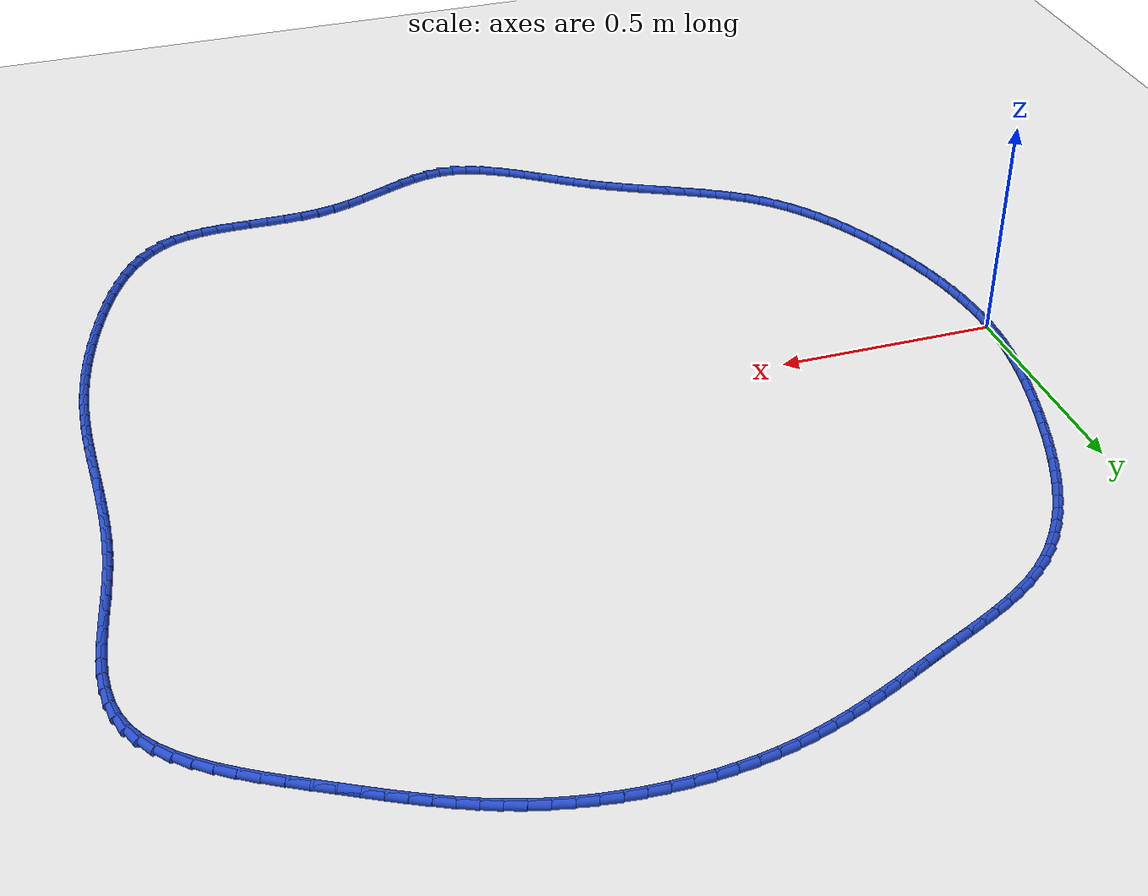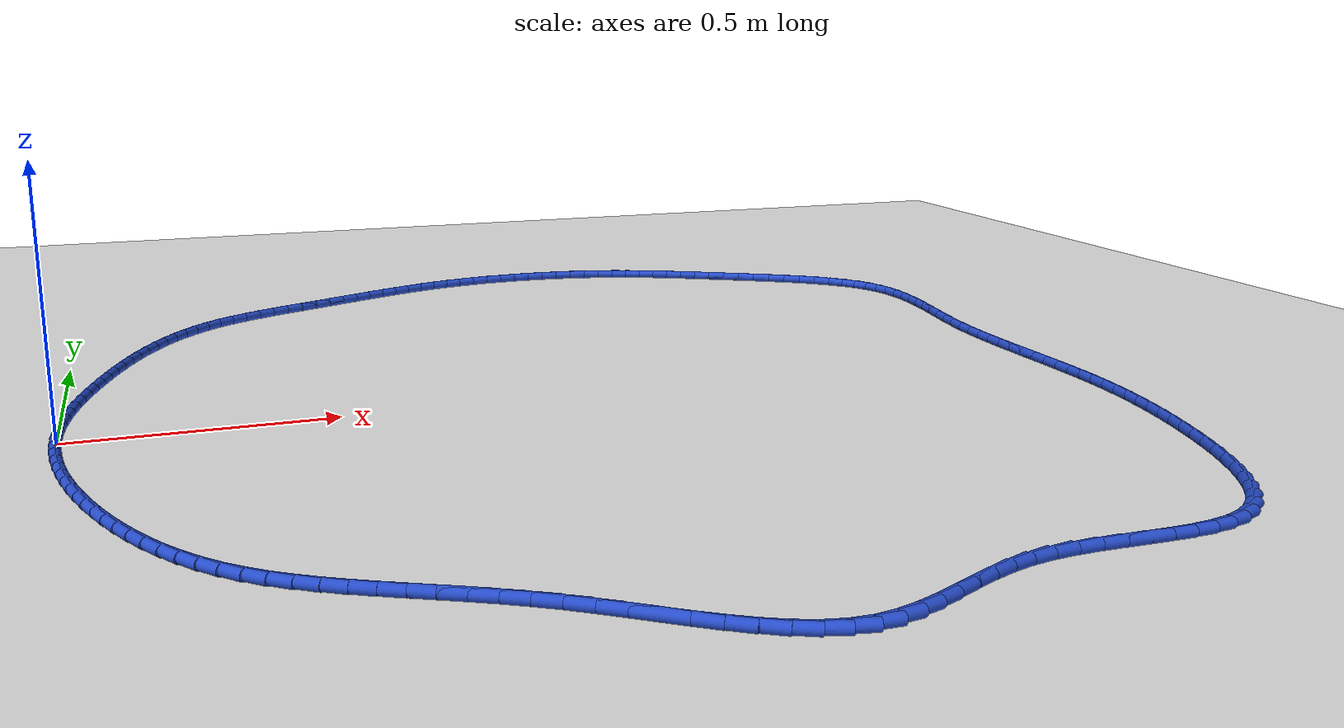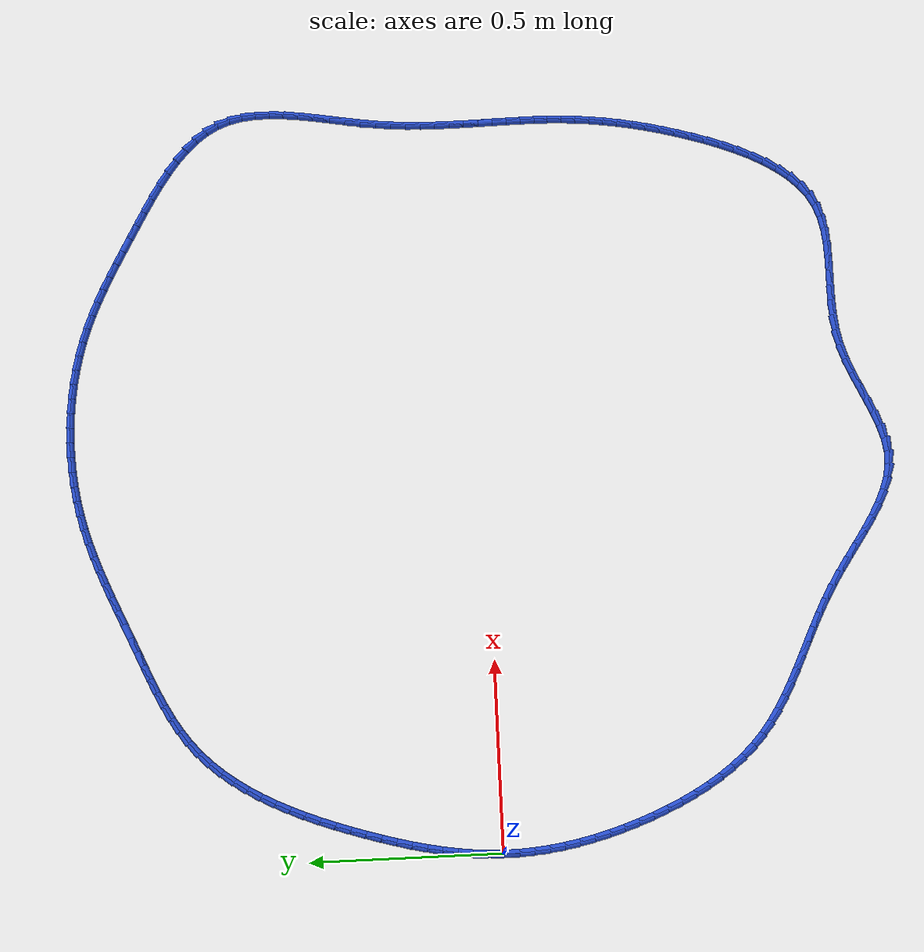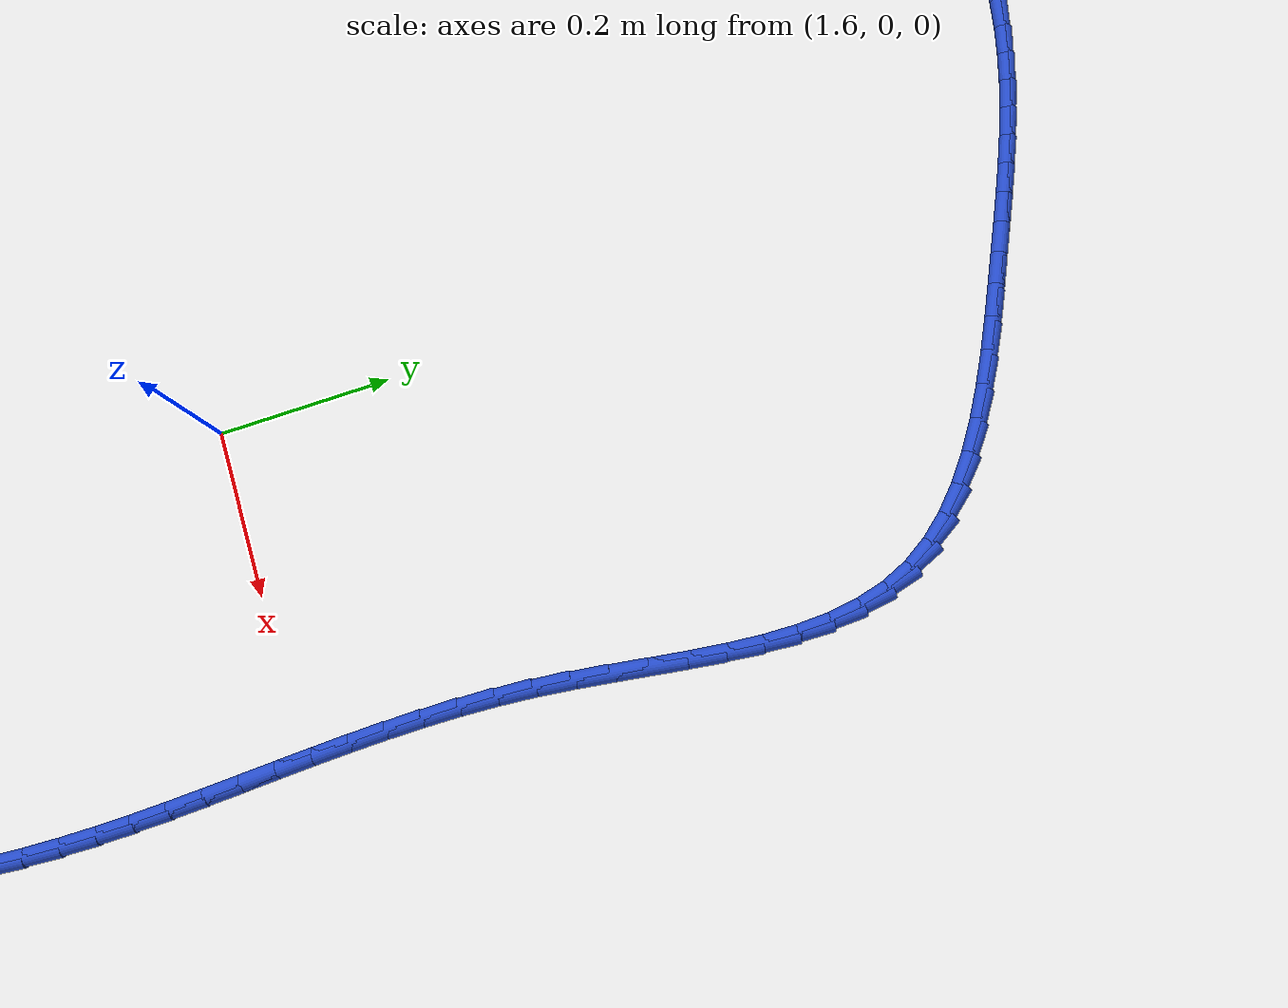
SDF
<sdf version="1.6">
 <world name="default">
  <light name="sun" type="directional">
   <pose>0 0 10 0 -0 0</pose>
   <diffuse>0.8 0.8 0.8 1</diffuse>
   <specular>0.2 0.2 0.2 1</specular>
   <attenuation>
    <range>1000</range>
    <constant>0.9</constant>
    <linear>0.01</linear>
    <quadratic>0.001</quadratic>
   </attenuation>
   <direction>-0.5 0.1 -0.9</direction>
  </light>
  <model name="ground_plane">
   <static>1</static>
   <link name="link">
    <collision name="collision">
     <geometry><plane><normal>0 0 1</normal><size>100 100</size></plane></geometry>
     <surface><friction><ode><mu>100</mu><mu2>50</mu2></ode></friction></surface>
    </collision>
    <visual name="visual">
     <cast_shadows>0</cast_shadows>
     <geometry><plane><normal>0 0 1</normal><size>100 100</size></plane></geometry>
     <material>
      <script><uri>file://media/materials/scripts/gazebo.material</uri><name>Gazebo/WhiteGlow</name></script>
     </material>
    </visual>
   </link>
  </model>
  <gravity>0 0 -9.8</gravity>
  <magnetic_field>6e-06 2.3e-05 -4.2e-05</magnetic_field>
  <atmosphere type="adiabatic"/>
  <physics name="default_physics" default="0" type="ode">
   <max_step_size>0.001</max_step_size>
   <real_time_factor>1</real_time_factor>
   <real_time_update_rate>1000</real_time_update_rate>
  </physics>
  <scene><ambient>0.4 0.4 0.4 1</ambient><background>0.7 0.7 0.7 1</background><shadows>1</shadows></scene>
  <spherical_coordinates>
   <surface_model>EARTH_WGS84</surface_model>
   <latitude_deg>0</latitude_deg>
   <longitude_deg>0</longitude_deg>
   <elevation>0</elevation>
   <heading_deg>0</heading_deg>
  </spherical_coordinates>
  <model name="line">
   <link name="link_0">
    <pose>-8.673617379884035e-18 -6.938893903907228e-18 0.01 0 1.57 1.5354247967208827</pose>
    <collision name="collision">
     <geometry><cylinder><radius>0.01</radius><length>0.08</length></cylinder></geometry>
    </collision>
    <visual name="visual">
     <material>
      <script><name>Gazebo/Blue</name><uri>file://media/materials/scripts/gazebo.material</uri></script>
     </material>
     <geometry><cylinder><radius>0.01</radius><length>0.08</length></cylinder></geometry>
    </visual>
   </link>
   <link name="link_1">
    <pose>0.0013825050643212892 0.03906894730974229 0.01 0 1.57 1.4908828772308236</pose>
    <collision name="collision">
     <geometry><cylinder><radius>0.01</radius><length>0.08</length></cylinder></geometry>
    </collision>
    <visual name="visual">
     <material>
      <script><name>Gazebo/Blue</name><uri>file://media/materials/scripts/gazebo.material</uri></script>
     </material>
     <geometry><cylinder><radius>0.01</radius><length>0.08</length></cylinder></geometry>
    </visual>
   </link>
   <link name="link_2">
    <pose>0.004506165908271949 0.07807375350420086 0.01 0 1.57 1.4498264423140341</pose>
    <collision name="collision">
     <geometry><cylinder><radius>0.01</radius><length>0.08</length></cylinder></geometry>
    </collision>
    <visual name="visual">
     <material>
      <script><name>Gazebo/Blue</name><uri>file://media/materials/scripts/gazebo.material</uri></script>
     </material>
     <geometry><cylinder><radius>0.01</radius><length>0.08</length></cylinder></geometry>
    </visual>
   </link>
   <link name="link_3">
    <pose>0.009242213815881412 0.11703322982333247 0.01 0 1.57 1.4123816714214383</pose>
    <collision name="collision">
     <geometry><cylinder><radius>0.01</radius><length>0.08</length></cylinder></geometry>
    </collision>
    <visual name="visual">
     <material>
      <script><name>Gazebo/Blue</name><uri>file://media/materials/scripts/gazebo.material</uri></script>
     </material>
     <geometry><cylinder><radius>0.01</radius><length>0.08</length></cylinder></geometry>
    </visual>
   </link>
   <link name="link_4">
    <pose>0.015461880071179107 0.1559661875070941 0.01 0 1.57 1.3786067874616756</pose>
    <collision name="collision">
     <geometry><cylinder><radius>0.01</radius><length>0.08</length></cylinder></geometry>
    </collision>
    <visual name="visual">
     <material>
      <script><name>Gazebo/Blue</name><uri>file://media/materials/scripts/gazebo.material</uri></script>
     </material>
     <geometry><cylinder><radius>0.01</radius><length>0.08</length></cylinder></geometry>
    </visual>
   </link>
   <link name="link_5">
    <pose>0.023036395958194462 0.19489143779544235 0.01 0 1.57 1.34850630927568</pose>
    <collision name="collision">
     <geometry><cylinder><radius>0.01</radius><length>0.08</length></cylinder></geometry>
    </collision>
    <visual name="visual">
     <material>
      <script><name>Gazebo/Blue</name><uri>file://media/materials/scripts/gazebo.material</uri></script>
     </material>
     <geometry><cylinder><radius>0.01</radius><length>0.08</length></cylinder></geometry>
    </visual>
   </link>
   <link name="link_6">
    <pose>0.03183699276095692 0.2338277919283341 0.01 0 1.57 1.3220450251470515</pose>
    <collision name="collision">
     <geometry><cylinder><radius>0.01</radius><length>0.08</length></cylinder></geometry>
    </collision>
    <visual name="visual">
     <material>
      <script><name>Gazebo/Blue</name><uri>file://media/materials/scripts/gazebo.material</uri></script>
     </material>
     <geometry><cylinder><radius>0.01</radius><length>0.08</length></cylinder></geometry>
    </visual>
   </link>
   <link name="link_7">
    <pose>0.041734901763495875 0.2727940611457261 0.01 0 1.57 1.2991606508426912</pose>
    <collision name="collision">
     <geometry><cylinder><radius>0.01</radius><length>0.08</length></cylinder></geometry>
    </collision>
    <visual name="visual">
     <material>
      <script><name>Gazebo/Blue</name><uri>file://media/materials/scripts/gazebo.material</uri></script>
     </material>
     <geometry><cylinder><radius>0.01</radius><length>0.08</length></cylinder></geometry>
    </visual>
   </link>
   <link name="link_8">
    <pose>0.052601354249840804 0.3118090566875753 0.01 0 1.57 1.279774628854863</pose>
    <collision name="collision">
     <geometry><cylinder><radius>0.01</radius><length>0.08</length></cylinder></geometry>
    </collision>
    <visual name="visual">
     <material>
      <script><name>Gazebo/Blue</name><uri>file://media/materials/scripts/gazebo.material</uri></script>
     </material>
     <geometry><cylinder><radius>0.01</radius><length>0.08</length></cylinder></geometry>
    </visual>
   </link>
   <link name="link_9">
    <pose>0.06430758150402113 0.35089158979383833 0.01 0 1.57 1.263321220580942</pose>
    <collision name="collision">
     <geometry><cylinder><radius>0.01</radius><length>0.08</length></cylinder></geometry>
    </collision>
    <visual name="visual">
     <material>
      <script><name>Gazebo/Blue</name><uri>file://media/materials/scripts/gazebo.material</uri></script>
     </material>
     <geometry><cylinder><radius>0.01</radius><length>0.08</length></cylinder></geometry>
    </visual>
   </link>
   <link name="link_10">
    <pose>0.07674095066680027 0.3900461623906067 0.01 0 1.57 1.245324803403687</pose>
    <collision name="collision">
     <geometry><cylinder><radius>0.01</radius><length>0.08</length></cylinder></geometry>
    </collision>
    <visual name="visual">
     <material>
      <script><name>Gazebo/Blue</name><uri>file://media/materials/scripts/gazebo.material</uri></script>
     </material>
     <geometry><cylinder><radius>0.01</radius><length>0.08</length></cylinder></geometry>
    </visual>
   </link>
   <link name="link_11">
    <pose>0.08993626492081125 0.4291465297920647 0.01 0 1.57 1.2233031122250573</pose>
    <collision name="collision">
     <geometry><cylinder><radius>0.01</radius><length>0.08</length></cylinder></geometry>
    </collision>
    <visual name="visual">
     <material>
      <script><name>Gazebo/Blue</name><uri>file://media/materials/scripts/gazebo.material</uri></script>
     </material>
     <geometry><cylinder><radius>0.01</radius><length>0.08</length></cylinder></geometry>
    </visual>
   </link>
   <link name="link_12">
    <pose>0.10400731175838522 0.46799640384978175 0.01 0 1.57 1.1970347129776315</pose>
    <collision name="collision">
     <geometry><cylinder><radius>0.01</radius><length>0.08</length></cylinder></geometry>
    </collision>
    <visual name="visual">
     <material>
      <script><name>Gazebo/Blue</name><uri>file://media/materials/scripts/gazebo.material</uri></script>
     </material>
     <geometry><cylinder><radius>0.01</radius><length>0.08</length></cylinder></geometry>
    </visual>
   </link>
   <link name="link_13">
    <pose>0.11906862884791193 0.506398831157519 0.01 0 1.57 1.1662600544415076</pose>
    <collision name="collision">
     <geometry><cylinder><radius>0.01</radius><length>0.08</length></cylinder></geometry>
    </collision>
    <visual name="visual">
     <material>
      <script><name>Gazebo/Blue</name><uri>file://media/materials/scripts/gazebo.material</uri></script>
     </material>
     <geometry><cylinder><radius>0.01</radius><length>0.08</length></cylinder></geometry>
    </visual>
   </link>
   <link name="link_14">
    <pose>0.13523475385778116 0.544156858309038 0.01 0 1.57 1.1306672944568665</pose>
    <collision name="collision">
     <geometry><cylinder><radius>0.01</radius><length>0.08</length></cylinder></geometry>
    </collision>
    <visual name="visual">
     <material>
      <script><name>Gazebo/Blue</name><uri>file://media/materials/scripts/gazebo.material</uri></script>
     </material>
     <geometry><cylinder><radius>0.01</radius><length>0.08</length></cylinder></geometry>
    </visual>
   </link>
   <link name="link_15">
    <pose>0.15262022445638276 0.5810735318981 0.01 0 1.57 1.0899045323295076</pose>
    <collision name="collision">
     <geometry><cylinder><radius>0.01</radius><length>0.08</length></cylinder></geometry>
    </collision>
    <visual name="visual">
     <material>
      <script><name>Gazebo/Blue</name><uri>file://media/materials/scripts/gazebo.material</uri></script>
     </material>
     <geometry><cylinder><radius>0.01</radius><length>0.08</length></cylinder></geometry>
    </visual>
   </link>
   <link name="link_16">
    <pose>0.17133957831210658 0.6169518985184664 0.01 0 1.57 1.0435989721002894</pose>
    <collision name="collision">
     <geometry><cylinder><radius>0.01</radius><length>0.08</length></cylinder></geometry>
    </collision>
    <visual name="visual">
     <material>
      <script><name>Gazebo/Blue</name><uri>file://media/materials/scripts/gazebo.material</uri></script>
     </material>
     <geometry><cylinder><radius>0.01</radius><length>0.08</length></cylinder></geometry>
    </visual>
   </link>
   <link name="link_17">
    <pose>0.19150735309334233 0.6515950047638986 0.01 0 1.57 0.9913863497934005</pose>
    <collision name="collision">
     <geometry><cylinder><radius>0.01</radius><length>0.08</length></cylinder></geometry>
    </collision>
    <visual name="visual">
     <material>
      <script><name>Gazebo/Blue</name><uri>file://media/materials/scripts/gazebo.material</uri></script>
     </material>
     <geometry><cylinder><radius>0.01</radius><length>0.08</length></cylinder></geometry>
    </visual>
   </link>
   <link name="link_18">
    <pose>0.21323808646847983 0.684805897228158 0.01 0 1.57 0.9329540142925298</pose>
    <collision name="collision">
     <geometry><cylinder><radius>0.01</radius><length>0.08</length></cylinder></geometry>
    </collision>
    <visual name="visual">
     <material>
      <script><name>Gazebo/Blue</name><uri>file://media/materials/scripts/gazebo.material</uri></script>
     </material>
     <geometry><cylinder><radius>0.01</radius><length>0.08</length></cylinder></geometry>
    </visual>
   </link>
   <link name="link_19">
    <pose>0.2366463161059089 0.716387622505006 0.01 0 1.57 0.8680999923756387</pose>
    <collision name="collision">
     <geometry><cylinder><radius>0.01</radius><length>0.08</length></cylinder></geometry>
    </collision>
    <visual name="visual">
     <material>
      <script><name>Gazebo/Blue</name><uri>file://media/materials/scripts/gazebo.material</uri></script>
     </material>
     <geometry><cylinder><radius>0.01</radius><length>0.08</length></cylinder></geometry>
    </visual>
   </link>
   <link name="link_20">
    <pose>0.26184657967401925 0.7461432271882036 0.01 0 1.57 0.7968072735817116</pose>
    <collision name="collision">
     <geometry><cylinder><radius>0.01</radius><length>0.08</length></cylinder></geometry>
    </collision>
    <visual name="visual">
     <material>
      <script><name>Gazebo/Blue</name><uri>file://media/materials/scripts/gazebo.material</uri></script>
     </material>
     <geometry><cylinder><radius>0.01</radius><length>0.08</length></cylinder></geometry>
    </visual>
   </link>
   <link name="link_21">
    <pose>0.28895341484120096 0.7738757578715129 0.01 0 1.57 0.7193332785388655</pose>
    <collision name="collision">
     <geometry><cylinder><radius>0.01</radius><length>0.08</length></cylinder></geometry>
    </collision>
    <visual name="visual">
     <material>
      <script><name>Gazebo/Blue</name><uri>file://media/materials/scripts/gazebo.material</uri></script>
     </material>
     <geometry><cylinder><radius>0.01</radius><length>0.08</length></cylinder></geometry>
    </visual>
   </link>
   <link name="link_22">
    <pose>0.31808119799682333 0.7993884625396205 0.01 0 1.57 0.640544846958888</pose>
    <collision name="collision">
     <geometry><cylinder><radius>0.01</radius><length>0.08</length></cylinder></geometry>
    </collision>
    <visual name="visual">
     <material>
      <script><name>Gazebo/Blue</name><uri>file://media/materials/scripts/gazebo.material</uri></script>
     </material>
     <geometry><cylinder><radius>0.01</radius><length>0.08</length></cylinder></geometry>
    </visual>
   </link>
   <link name="link_23">
    <pose>0.34924044235251633 0.8226142842953275 0.01 0 1.57 0.5726735221452041</pose>
    <collision name="collision">
     <geometry><cylinder><radius>0.01</radius><length>0.08</length></cylinder></geometry>
    </collision>
    <visual name="visual">
     <material>
      <script><name>Gazebo/Blue</name><uri>file://media/materials/scripts/gazebo.material</uri></script>
     </material>
     <geometry><cylinder><radius>0.01</radius><length>0.08</length></cylinder></geometry>
    </visual>
   </link>
   <link name="link_24">
    <pose>0.3821593720415288 0.8438386637882926 0.01 0 1.57 0.5176922530987258</pose>
    <collision name="collision">
     <geometry><cylinder><radius>0.01</radius><length>0.08</length></cylinder></geometry>
    </collision>
    <visual name="visual">
     <material>
      <script><name>Gazebo/Blue</name><uri>file://media/materials/scripts/gazebo.material</uri></script>
     </material>
     <geometry><cylinder><radius>0.01</radius><length>0.08</length></cylinder></geometry>
    </visual>
   </link>
   <link name="link_25">
    <pose>0.4165187077536712 0.8634063597522318 0.01 0 1.57 0.47520412315674315</pose>
    <collision name="collision">
     <geometry><cylinder><radius>0.01</radius><length>0.08</length></cylinder></geometry>
    </collision>
    <visual name="visual">
     <material>
      <script><name>Gazebo/Blue</name><uri>file://media/materials/scripts/gazebo.material</uri></script>
     </material>
     <geometry><cylinder><radius>0.01</radius><length>0.08</length></cylinder></geometry>
    </visual>
   </link>
   <link name="link_26">
    <pose>0.45199917017875396 0.8816621309208603 0.01 0 1.57 0.4446733875477434</pose>
    <collision name="collision">
     <geometry><cylinder><radius>0.01</radius><length>0.08</length></cylinder></geometry>
    </collision>
    <visual name="visual">
     <material>
      <script><name>Gazebo/Blue</name><uri>file://media/materials/scripts/gazebo.material</uri></script>
     </material>
     <geometry><cylinder><radius>0.01</radius><length>0.08</length></cylinder></geometry>
    </visual>
   </link>
   <link name="link_27">
    <pose>0.4882814800065874 0.8989507360278943 0.01 0 1.57 0.4256101290940283</pose>
    <collision name="collision">
     <geometry><cylinder><radius>0.01</radius><length>0.08</length></cylinder></geometry>
    </collision>
    <visual name="visual">
     <material>
      <script><name>Gazebo/Blue</name><uri>file://media/materials/scripts/gazebo.material</uri></script>
     </material>
     <geometry><cylinder><radius>0.01</radius><length>0.08</length></cylinder></geometry>
    </visual>
   </link>
   <link name="link_28">
    <pose>0.5250463579269822 0.9156169338070489 0.01 0 1.57 0.4176821834317613</pose>
    <collision name="collision">
     <geometry><cylinder><radius>0.01</radius><length>0.08</length></cylinder></geometry>
    </collision>
    <visual name="visual">
     <material>
      <script><name>Gazebo/Blue</name><uri>file://media/materials/scripts/gazebo.material</uri></script>
     </material>
     <geometry><cylinder><radius>0.01</radius><length>0.08</length></cylinder></geometry>
    </visual>
   </link>
   <link name="link_29">
    <pose>0.5619745246297484 0.9320054829920398 0.01 0 1.57 0.4203912868727868</pose>
    <collision name="collision">
     <geometry><cylinder><radius>0.01</radius><length>0.08</length></cylinder></geometry>
    </collision>
    <visual name="visual">
     <material>
      <script><name>Gazebo/Blue</name><uri>file://media/materials/scripts/gazebo.material</uri></script>
     </material>
     <geometry><cylinder><radius>0.01</radius><length>0.08</length></cylinder></geometry>
    </visual>
   </link>
   <link name="link_30">
    <pose>0.5987564832216699 0.9484485614264324 0.01 0 1.57 0.4255999580675025</pose>
    <collision name="collision">
     <geometry><cylinder><radius>0.01</radius><length>0.08</length></cylinder></geometry>
    </collision>
    <visual name="visual">
     <material>
      <script><name>Gazebo/Blue</name><uri>file://media/materials/scripts/gazebo.material</uri></script>
     </material>
     <geometry><cylinder><radius>0.01</radius><length>0.08</length></cylinder></geometry>
    </visual>
   </link>
   <link name="link_31">
    <pose>0.6352913571693464 0.9650100462018243 0.01 0 1.57 0.42542437116408216</pose>
    <collision name="collision">
     <geometry><cylinder><radius>0.01</radius><length>0.08</length></cylinder></geometry>
    </collision>
    <visual name="visual">
     <material>
      <script><name>Gazebo/Blue</name><uri>file://media/materials/scripts/gazebo.material</uri></script>
     </material>
     <geometry><cylinder><radius>0.01</radius><length>0.08</length></cylinder></geometry>
    </visual>
   </link>
   <link name="link_32">
    <pose>0.671678179160152 0.9814967168077061 0.01 0 1.57 0.4194778309859588</pose>
    <collision name="collision">
     <geometry><cylinder><radius>0.01</radius><length>0.08</length></cylinder></geometry>
    </collision>
    <visual name="visual">
     <material>
      <script><name>Gazebo/Blue</name><uri>file://media/materials/scripts/gazebo.material</uri></script>
     </material>
     <geometry><cylinder><radius>0.01</radius><length>0.08</length></cylinder></geometry>
    </visual>
   </link>
   <link name="link_33">
    <pose>0.7080240210769684 0.9977050137513073 0.01 0 1.57 0.40770161124175586</pose>
    <collision name="collision">
     <geometry><cylinder><radius>0.01</radius><length>0.08</length></cylinder></geometry>
    </collision>
    <visual name="visual">
     <material>
      <script><name>Gazebo/Blue</name><uri>file://media/materials/scripts/gazebo.material</uri></script>
     </material>
     <geometry><cylinder><radius>0.01</radius><length>0.08</length></cylinder></geometry>
    </visual>
   </link>
   <link name="link_34">
    <pose>0.7444359548026763 1.013431377539857 0.01 0 1.57 0.3900558137274472</pose>
    <collision name="collision">
     <geometry><cylinder><radius>0.01</radius><length>0.08</length></cylinder></geometry>
    </collision>
    <visual name="visual">
     <material>
      <script><name>Gazebo/Blue</name><uri>file://media/materials/scripts/gazebo.material</uri></script>
     </material>
     <geometry><cylinder><radius>0.01</radius><length>0.08</length></cylinder></geometry>
    </visual>
   </link>
   <link name="link_35">
    <pose>0.7810210522201568 1.0284722486805846 0.01 0 1.57 0.3665319929024972</pose>
    <collision name="collision">
     <geometry><cylinder><radius>0.01</radius><length>0.08</length></cylinder></geometry>
    </collision>
    <visual name="visual">
     <material>
      <script><name>Gazebo/Blue</name><uri>file://media/materials/scripts/gazebo.material</uri></script>
     </material>
     <geometry><cylinder><radius>0.01</radius><length>0.08</length></cylinder></geometry>
    </visual>
   </link>
   <link name="link_36">
    <pose>0.8178863852122915 1.042624067680719 0.01 0 1.57 0.3371717475668444</pose>
    <collision name="collision">
     <geometry><cylinder><radius>0.01</radius><length>0.08</length></cylinder></geometry>
    </collision>
    <visual name="visual">
     <material>
      <script><name>Gazebo/Blue</name><uri>file://media/materials/scripts/gazebo.material</uri></script>
     </material>
     <geometry><cylinder><radius>0.01</radius><length>0.08</length></cylinder></geometry>
    </visual>
   </link>
   <link name="link_37">
    <pose>0.8551390256619612 1.05568327504749 0.01 0 1.57 0.3020904434956613</pose>
    <collision name="collision">
     <geometry><cylinder><radius>0.01</radius><length>0.08</length></cylinder></geometry>
    </collision>
    <visual name="visual">
     <material>
      <script><name>Gazebo/Blue</name><uri>file://media/materials/scripts/gazebo.material</uri></script>
     </material>
     <geometry><cylinder><radius>0.01</radius><length>0.08</length></cylinder></geometry>
    </visual>
   </link>
   <link name="link_38">
    <pose>0.8928860454520464 1.067446311288126 0.01 0 1.57 0.2615043488212305</pose>
    <collision name="collision">
     <geometry><cylinder><radius>0.01</radius><length>0.08</length></cylinder></geometry>
    </collision>
    <visual name="visual">
     <material>
      <script><name>Gazebo/Blue</name><uri>file://media/materials/scripts/gazebo.material</uri></script>
     </material>
     <geometry><cylinder><radius>0.01</radius><length>0.08</length></cylinder></geometry>
    </visual>
   </link>
   <link name="link_39">
    <pose>0.9312345070458207 1.077709624940949 0.01 0 1.57 0.2169953253717377</pose>
    <collision name="collision">
     <geometry><cylinder><radius>0.01</radius><length>0.08</length></cylinder></geometry>
    </collision>
    <visual name="visual">
     <material>
      <script><name>Gazebo/Blue</name><uri>file://media/materials/scripts/gazebo.material</uri></script>
     </material>
     <geometry><cylinder><radius>0.01</radius><length>0.08</length></cylinder></geometry>
    </visual>
   </link>
   <link name="link_40">
    <pose>0.9702442089245338 1.086309961479969 0.01 0 1.57 0.17281984940199646</pose>
    <collision name="collision">
     <geometry><cylinder><radius>0.01</radius><length>0.08</length></cylinder></geometry>
    </collision>
    <visual name="visual">
     <material>
      <script><name>Gazebo/Blue</name><uri>file://media/materials/scripts/gazebo.material</uri></script>
     </material>
     <geometry><cylinder><radius>0.01</radius><length>0.08</length></cylinder></geometry>
    </visual>
   </link>
   <link name="link_41">
    <pose>1.0098178749165594 1.0932179871136565 0.01 0 1.57 0.12959836551009693</pose>
    <collision name="collision">
     <geometry><cylinder><radius>0.01</radius><length>0.08</length></cylinder></geometry>
    </collision>
    <visual name="visual">
     <material>
      <script><name>Gazebo/Blue</name><uri>file://media/materials/scripts/gazebo.material</uri></script>
     </material>
     <geometry><cylinder><radius>0.01</radius><length>0.08</length></cylinder></geometry>
    </visual>
   </link>
   <link name="link_42">
    <pose>1.0498256403466943 1.0984321527773817 0.01 0 1.57 0.08706738772862936</pose>
    <collision name="collision">
     <geometry><cylinder><radius>0.01</radius><length>0.08</length></cylinder></geometry>
    </collision>
    <visual name="visual">
     <material>
      <script><name>Gazebo/Blue</name><uri>file://media/materials/scripts/gazebo.material</uri></script>
     </material>
     <geometry><cylinder><radius>0.01</radius><length>0.08</length></cylinder></geometry>
    </visual>
   </link>
   <link name="link_43">
    <pose>1.0901376405397374 1.1019509094065185 0.01 0 1.57 0.04496748940232887</pose>
    <collision name="collision">
     <geometry><cylinder><radius>0.01</radius><length>0.08</length></cylinder></geometry>
    </collision>
    <visual name="visual">
     <material>
      <script><name>Gazebo/Blue</name><uri>file://media/materials/scripts/gazebo.material</uri></script>
     </material>
     <geometry><cylinder><radius>0.01</radius><length>0.08</length></cylinder></geometry>
    </visual>
   </link>
   <link name="link_44">
    <pose>1.1306240108204861 1.1037727079364377 0.01 0 1.57 0.003041902837933673</pose>
    <collision name="collision">
     <geometry><cylinder><radius>0.01</radius><length>0.08</length></cylinder></geometry>
    </collision>
    <visual name="visual">
     <material>
      <script><name>Gazebo/Blue</name><uri>file://media/materials/scripts/gazebo.material</uri></script>
     </material>
     <geometry><cylinder><radius>0.01</radius><length>0.08</length></cylinder></geometry>
    </visual>
   </link>
   <link name="link_45">
    <pose>1.171154886513739 1.103895999302512 0.01 0 1.57 -0.038965179030784</pose>
    <collision name="collision">
     <geometry><cylinder><radius>0.01</radius><length>0.08</length></cylinder></geometry>
    </collision>
    <visual name="visual">
     <material>
      <script><name>Gazebo/Blue</name><uri>file://media/materials/scripts/gazebo.material</uri></script>
     </material>
     <geometry><cylinder><radius>0.01</radius><length>0.08</length></cylinder></geometry>
    </visual>
   </link>
   <link name="link_46">
    <pose>1.2116004029442922 1.1023192344401131 0.01 0 1.57 -0.08131042333278853</pose>
    <collision name="collision">
     <geometry><cylinder><radius>0.01</radius><length>0.08</length></cylinder></geometry>
    </collision>
    <visual name="visual">
     <material>
      <script><name>Gazebo/Blue</name><uri>file://media/materials/scripts/gazebo.material</uri></script>
     </material>
     <geometry><cylinder><radius>0.01</radius><length>0.08</length></cylinder></geometry>
    </visual>
   </link>
   <link name="link_47">
    <pose>1.2518306954369451 1.099040864284613 0.01 0 1.57 -0.12425313855654954</pose>
    <collision name="collision">
     <geometry><cylinder><radius>0.01</radius><length>0.08</length></cylinder></geometry>
    </collision>
    <visual name="visual">
     <material>
      <script><name>Gazebo/Blue</name><uri>file://media/materials/scripts/gazebo.material</uri></script>
     </material>
     <geometry><cylinder><radius>0.01</radius><length>0.08</length></cylinder></geometry>
    </visual>
   </link>
   <link name="link_48">
    <pose>1.2917158993164943 1.0940593397713836 0.01 0 1.57 -0.1680568477869703</pose>
    <collision name="collision">
     <geometry><cylinder><radius>0.01</radius><length>0.08</length></cylinder></geometry>
    </collision>
    <visual name="visual">
     <material>
      <script><name>Gazebo/Blue</name><uri>file://media/materials/scripts/gazebo.material</uri></script>
     </material>
     <geometry><cylinder><radius>0.01</radius><length>0.08</length></cylinder></geometry>
    </visual>
   </link>
   <link name="link_49">
    <pose>1.3311261499077385 1.0873731118357974 0.01 0 1.57 -0.2129904571610945</pose>
    <collision name="collision">
     <geometry><cylinder><radius>0.01</radius><length>0.08</length></cylinder></geometry>
    </collision>
    <visual name="visual">
     <material>
      <script><name>Gazebo/Blue</name><uri>file://media/materials/scripts/gazebo.material</uri></script>
     </material>
     <geometry><cylinder><radius>0.01</radius><length>0.08</length></cylinder></geometry>
    </visual>
   </link>
   <link name="link_50">
    <pose>1.3699315825354756 1.0789806314132264 0.01 0 1.57 -0.25932877304138785</pose>
    <collision name="collision">
     <geometry><cylinder><radius>0.01</radius><length>0.08</length></cylinder></geometry>
    </collision>
    <visual name="visual">
     <material>
      <script><name>Gazebo/Blue</name><uri>file://media/materials/scripts/gazebo.material</uri></script>
     </material>
     <geometry><cylinder><radius>0.01</radius><length>0.08</length></cylinder></geometry>
    </visual>
   </link>
   <link name="link_51">
    <pose>1.4080023325245028 1.0688803494390424 0.01 0 1.57 -0.3070932277901556</pose>
    <collision name="collision">
     <geometry><cylinder><radius>0.01</radius><length>0.08</length></cylinder></geometry>
    </collision>
    <visual name="visual">
     <material>
      <script><name>Gazebo/Blue</name><uri>file://media/materials/scripts/gazebo.material</uri></script>
     </material>
     <geometry><cylinder><radius>0.01</radius><length>0.08</length></cylinder></geometry>
    </visual>
   </link>
   <link name="link_52">
    <pose>1.4452216622945886 1.057077153023726 0.01 0 1.57 -0.3525371537069398</pose>
    <collision name="collision">
     <geometry><cylinder><radius>0.01</radius><length>0.08</length></cylinder></geometry>
    </collision>
    <visual name="visual">
     <material>
      <script><name>Gazebo/Blue</name><uri>file://media/materials/scripts/gazebo.material</uri></script>
     </material>
     <geometry><cylinder><radius>0.01</radius><length>0.08</length></cylinder></geometry>
    </visual>
   </link>
   <link name="link_53">
    <pose>1.4816641480213903 1.0436697298357969 0.01 0 1.57 -0.39217549380556954</pose>
    <collision name="collision">
     <geometry><cylinder><radius>0.01</radius><length>0.08</length></cylinder></geometry>
    </collision>
    <visual name="visual">
     <material>
      <script><name>Gazebo/Blue</name><uri>file://media/materials/scripts/gazebo.material</uri></script>
     </material>
     <geometry><cylinder><radius>0.01</radius><length>0.08</length></cylinder></geometry>
    </visual>
   </link>
   <link name="link_54">
    <pose>1.5175490708155777 1.0288277159373782 0.01 0 1.57 -0.4253684738614518</pose>
    <collision name="collision">
     <geometry><cylinder><radius>0.01</radius><length>0.08</length></cylinder></geometry>
    </collision>
    <visual name="visual">
     <material>
      <script><name>Gazebo/Blue</name><uri>file://media/materials/scripts/gazebo.material</uri></script>
     </material>
     <geometry><cylinder><radius>0.01</radius><length>0.08</length></cylinder></geometry>
    </visual>
   </link>
   <link name="link_55">
    <pose>1.5530992887042487 1.0127225011419412 0.01 0 1.57 -0.45179084007981357</pose>
    <collision name="collision">
     <geometry><cylinder><radius>0.01</radius><length>0.08</length></cylinder></geometry>
    </collision>
    <visual name="visual">
     <material>
      <script><name>Gazebo/Blue</name><uri>file://media/materials/scripts/gazebo.material</uri></script>
     </material>
     <geometry><cylinder><radius>0.01</radius><length>0.08</length></cylinder></geometry>
    </visual>
   </link>
   <link name="link_56">
    <pose>1.5885376597144985 0.9955254752629552 0.01 0 1.57 -0.4713311749989829</pose>
    <collision name="collision">
     <geometry><cylinder><radius>0.01</radius><length>0.08</length></cylinder></geometry>
    </collision>
    <visual name="visual">
     <material>
      <script><name>Gazebo/Blue</name><uri>file://media/materials/scripts/gazebo.material</uri></script>
     </material>
     <geometry><cylinder><radius>0.01</radius><length>0.08</length></cylinder></geometry>
    </visual>
   </link>
   <link name="link_57">
    <pose>1.6240870418734241 0.9774080281138912 0.01 0 1.57 -0.4840535263988768</pose>
    <collision name="collision">
     <geometry><cylinder><radius>0.01</radius><length>0.08</length></cylinder></geometry>
    </collision>
    <visual name="visual">
     <material>
      <script><name>Gazebo/Blue</name><uri>file://media/materials/scripts/gazebo.material</uri></script>
     </material>
     <geometry><cylinder><radius>0.01</radius><length>0.08</length></cylinder></geometry>
    </visual>
   </link>
   <link name="link_58">
    <pose>1.6599702932081228 0.9585415495082187 0.01 0 1.57 -0.4901595264899199</pose>
    <collision name="collision">
     <geometry><cylinder><radius>0.01</radius><length>0.08</length></cylinder></geometry>
    </collision>
    <visual name="visual">
     <material>
      <script><name>Gazebo/Blue</name><uri>file://media/materials/scripts/gazebo.material</uri></script>
     </material>
     <geometry><cylinder><radius>0.01</radius><length>0.08</length></cylinder></geometry>
    </visual>
   </link>
   <link name="link_59">
    <pose>1.6964102717456917 0.9390974292594089 0.01 0 1.57 -0.4907636424211257</pose>
    <collision name="collision">
     <geometry><cylinder><radius>0.01</radius><length>0.08</length></cylinder></geometry>
    </collision>
    <visual name="visual">
     <material>
      <script><name>Gazebo/Blue</name><uri>file://media/materials/scripts/gazebo.material</uri></script>
     </material>
     <geometry><cylinder><radius>0.01</radius><length>0.08</length></cylinder></geometry>
    </visual>
   </link>
   <link name="link_60">
    <pose>1.7335895550634075 0.919229956176513 0.01 0 1.57 -0.4958115956384678</pose>
    <collision name="collision">
     <geometry><cylinder><radius>0.01</radius><length>0.08</length></cylinder></geometry>
    </collision>
    <visual name="visual">
     <material>
      <script><name>Gazebo/Blue</name><uri>file://media/materials/scripts/gazebo.material</uri></script>
     </material>
     <geometry><cylinder><radius>0.01</radius><length>0.08</length></cylinder></geometry>
    </visual>
   </link>
   <link name="link_61">
    <pose>1.7712023489460587 0.8988860815582352 0.01 0 1.57 -0.5116781465560379</pose>
    <collision name="collision">
     <geometry><cylinder><radius>0.01</radius><length>0.08</length></cylinder></geometry>
    </collision>
    <visual name="visual">
     <material>
      <script><name>Gazebo/Blue</name><uri>file://media/materials/scripts/gazebo.material</uri></script>
     </material>
     <geometry><cylinder><radius>0.01</radius><length>0.08</length></cylinder></geometry>
    </visual>
   </link>
   <link name="link_62">
    <pose>1.8086179602419967 0.8778748213482268 0.01 0 1.57 -0.5388704966634605</pose>
    <collision name="collision">
     <geometry><cylinder><radius>0.01</radius><length>0.08</length></cylinder></geometry>
    </collision>
    <visual name="visual">
     <material>
      <script><name>Gazebo/Blue</name><uri>file://media/materials/scripts/gazebo.material</uri></script>
     </material>
     <geometry><cylinder><radius>0.01</radius><length>0.08</length></cylinder></geometry>
    </visual>
   </link>
   <link name="link_63">
    <pose>1.8451998220121644 0.8560026977825225 0.01 0 1.57 -0.5784538508213279</pose>
    <collision name="collision">
     <geometry><cylinder><radius>0.01</radius><length>0.08</length></cylinder></geometry>
    </collision>
    <visual name="visual">
     <material>
      <script><name>Gazebo/Blue</name><uri>file://media/materials/scripts/gazebo.material</uri></script>
     </material>
     <geometry><cylinder><radius>0.01</radius><length>0.08</length></cylinder></geometry>
    </visual>
   </link>
   <link name="link_64">
    <pose>1.8803113673175027 0.8330762330971592 0.01 0 1.57 -0.632174544895152</pose>
    <collision name="collision">
     <geometry><cylinder><radius>0.01</radius><length>0.08</length></cylinder></geometry>
    </collision>
    <visual name="visual">
     <material>
      <script><name>Gazebo/Blue</name><uri>file://media/materials/scripts/gazebo.material</uri></script>
     </material>
     <geometry><cylinder><radius>0.01</radius><length>0.08</length></cylinder></geometry>
    </visual>
   </link>
   <link name="link_65">
    <pose>1.9133160292189546 0.8089019495281721 0.01 0 1.57 -0.7024483147444581</pose>
    <collision name="collision">
     <geometry><cylinder><radius>0.01</radius><length>0.08</length></cylinder></geometry>
    </collision>
    <visual name="visual">
     <material>
      <script><name>Gazebo/Blue</name><uri>file://media/materials/scripts/gazebo.material</uri></script>
     </material>
     <geometry><cylinder><radius>0.01</radius><length>0.08</length></cylinder></geometry>
    </visual>
   </link>
   <link name="link_66">
    <pose>1.9435772407774625 0.7832863693115967 0.01 0 1.57 -0.79221774710163</pose>
    <collision name="collision">
     <geometry><cylinder><radius>0.01</radius><length>0.08</length></cylinder></geometry>
    </collision>
    <visual name="visual">
     <material>
      <script><name>Gazebo/Blue</name><uri>file://media/materials/scripts/gazebo.material</uri></script>
     </material>
     <geometry><cylinder><radius>0.01</radius><length>0.08</length></cylinder></geometry>
    </visual>
   </link>
   <link name="link_67">
    <pose>1.9704584350539673 0.7560360146834694 0.01 0 1.57 -0.9044628898342737</pose>
    <collision name="collision">
     <geometry><cylinder><radius>0.01</radius><length>0.08</length></cylinder></geometry>
    </collision>
    <visual name="visual">
     <material>
      <script><name>Gazebo/Blue</name><uri>file://media/materials/scripts/gazebo.material</uri></script>
     </material>
     <geometry><cylinder><radius>0.01</radius><length>0.08</length></cylinder></geometry>
    </visual>
   </link>
   <link name="link_68">
    <pose>1.9933230451094133 0.7269574078798254 0.01 0 1.57 -1.0410538635224278</pose>
    <collision name="collision">
     <geometry><cylinder><radius>0.01</radius><length>0.08</length></cylinder></geometry>
    </collision>
    <visual name="visual">
     <material>
      <script><name>Gazebo/Blue</name><uri>file://media/materials/scripts/gazebo.material</uri></script>
     </material>
     <geometry><cylinder><radius>0.01</radius><length>0.08</length></cylinder></geometry>
    </visual>
   </link>
   <link name="link_69">
    <pose>2.011534504004741 0.6958570711367009 0.01 0 1.57 -1.196380597258871</pose>
    <collision name="collision">
     <geometry><cylinder><radius>0.01</radius><length>0.08</length></cylinder></geometry>
    </collision>
    <visual name="visual">
     <material>
      <script><name>Gazebo/Blue</name><uri>file://media/materials/scripts/gazebo.material</uri></script>
     </material>
     <geometry><cylinder><radius>0.01</radius><length>0.08</length></cylinder></geometry>
    </visual>
   </link>
   <link name="link_70">
    <pose>2.0246055262354012 0.6625934041407806 0.01 0 1.57 -1.3402567308373683</pose>
    <collision name="collision">
     <geometry><cylinder><radius>0.01</radius><length>0.08</length></cylinder></geometry>
    </collision>
    <visual name="visual">
     <material>
      <script><name>Gazebo/Blue</name><uri>file://media/materials/scripts/gazebo.material</uri></script>
     </material>
     <geometry><cylinder><radius>0.01</radius><length>0.08</length></cylinder></geometry>
    </visual>
   </link>
   <link name="link_71">
    <pose>2.032885666938521 0.6273156207662773 0.01 0 1.57 -1.4597518294533733</pose>
    <collision name="collision">
     <geometry><cylinder><radius>0.01</radius><length>0.08</length></cylinder></geometry>
    </collision>
    <visual name="visual">
     <material>
      <script><name>Gazebo/Blue</name><uri>file://media/materials/scripts/gazebo.material</uri></script>
     </material>
     <geometry><cylinder><radius>0.01</radius><length>0.08</length></cylinder></geometry>
    </visual>
   </link>
   <link name="link_72">
    <pose>2.037015902456795 0.5902742079576954 0.01 0 1.57 -1.5546749816541776</pose>
    <collision name="collision">
     <geometry><cylinder><radius>0.01</radius><length>0.08</length></cylinder></geometry>
    </collision>
    <visual name="visual">
     <material>
      <script><name>Gazebo/Blue</name><uri>file://media/materials/scripts/gazebo.material</uri></script>
     </material>
     <geometry><cylinder><radius>0.01</radius><length>0.08</length></cylinder></geometry>
    </visual>
   </link>
   <link name="link_73">
    <pose>2.037637505938731 0.5517197558038367 0.01 0 1.57 1.5144539579037297</pose>
    <collision name="collision">
     <geometry><cylinder><radius>0.01</radius><length>0.08</length></cylinder></geometry>
    </collision>
    <visual name="visual">
     <material>
      <script><name>Gazebo/Blue</name><uri>file://media/materials/scripts/gazebo.material</uri></script>
     </material>
     <geometry><cylinder><radius>0.01</radius><length>0.08</length></cylinder></geometry>
    </visual>
   </link>
   <link name="link_74">
    <pose>2.0353917505328405 0.5119028543935045 0.01 0 1.57 1.4617044236143706</pose>
    <collision name="collision">
     <geometry><cylinder><radius>0.01</radius><length>0.08</length></cylinder></geometry>
    </collision>
    <visual name="visual">
     <material>
      <script><name>Gazebo/Blue</name><uri>file://media/materials/scripts/gazebo.material</uri></script>
     </material>
     <geometry><cylinder><radius>0.01</radius><length>0.08</length></cylinder></geometry>
    </visual>
   </link>
   <link name="link_75">
    <pose>2.030919909387632 0.47107409381550225 0.01 0 1.57 1.4261853415969281</pose>
    <collision name="collision">
     <geometry><cylinder><radius>0.01</radius><length>0.08</length></cylinder></geometry>
    </collision>
    <visual name="visual">
     <material>
      <script><name>Gazebo/Blue</name><uri>file://media/materials/scripts/gazebo.material</uri></script>
     </material>
     <geometry><cylinder><radius>0.01</radius><length>0.08</length></cylinder></geometry>
    </visual>
   </link>
   <link name="link_76">
    <pose>2.0248632556516166 0.42948406415863283 0.01 0 1.57 1.40603111574253</pose>
    <collision name="collision">
     <geometry><cylinder><radius>0.01</radius><length>0.08</length></cylinder></geometry>
    </collision>
    <visual name="visual">
     <material>
      <script><name>Gazebo/Blue</name><uri>file://media/materials/scripts/gazebo.material</uri></script>
     </material>
     <geometry><cylinder><radius>0.01</radius><length>0.08</length></cylinder></geometry>
    </visual>
   </link>
   <link name="link_77">
    <pose>2.017863062473303 0.3873833555116989 0.01 0 1.57 1.4000869364141282</pose>
    <collision name="collision">
     <geometry><cylinder><radius>0.01</radius><length>0.08</length></cylinder></geometry>
    </collision>
    <visual name="visual">
     <material>
      <script><name>Gazebo/Blue</name><uri>file://media/materials/scripts/gazebo.material</uri></script>
     </material>
     <geometry><cylinder><radius>0.01</radius><length>0.08</length></cylinder></geometry>
    </visual>
   </link>
   <link name="link_78">
    <pose>2.010560603001202 0.34502255796350395 0.01 0 1.57 1.4079049732465845</pose>
    <collision name="collision">
     <geometry><cylinder><radius>0.01</radius><length>0.08</length></cylinder></geometry>
    </collision>
    <visual name="visual">
     <material>
      <script><name>Gazebo/Blue</name><uri>file://media/materials/scripts/gazebo.material</uri></script>
     </material>
     <geometry><cylinder><radius>0.01</radius><length>0.08</length></cylinder></geometry>
    </visual>
   </link>
   <link name="link_79">
    <pose>2.003597150383823 0.30265226160285075 0.01 0 1.57 1.429719966574659</pose>
    <collision name="collision">
     <geometry><cylinder><radius>0.01</radius><length>0.08</length></cylinder></geometry>
    </collision>
    <visual name="visual">
     <material>
      <script><name>Gazebo/Blue</name><uri>file://media/materials/scripts/gazebo.material</uri></script>
     </material>
     <geometry><cylinder><radius>0.01</radius><length>0.08</length></cylinder></geometry>
    </visual>
   </link>
   <link name="link_80">
    <pose>1.9976139687807322 0.2605230535309892 0.01 0 1.57 1.4627930545748875</pose>
    <collision name="collision">
     <geometry><cylinder><radius>0.01</radius><length>0.08</length></cylinder></geometry>
    </collision>
    <visual name="visual">
     <material>
      <script><name>Gazebo/Blue</name><uri>file://media/materials/scripts/gazebo.material</uri></script>
     </material>
     <geometry><cylinder><radius>0.01</radius><length>0.08</length></cylinder></geometry>
    </visual>
   </link>
   <link name="link_81">
    <pose>1.993093695386927 0.2188327997982529 0.01 0 1.57 1.4948596407253267</pose>
    <collision name="collision">
     <geometry><cylinder><radius>0.01</radius><length>0.08</length></cylinder></geometry>
    </collision>
    <visual name="visual">
     <material>
      <script><name>Gazebo/Blue</name><uri>file://media/materials/scripts/gazebo.material</uri></script>
     </material>
     <geometry><cylinder><radius>0.01</radius><length>0.08</length></cylinder></geometry>
    </visual>
   </link>
   <link name="link_82">
    <pose>1.989955991823093 0.17759225662785066 0.01 0 1.57 1.522811784377706</pose>
    <collision name="collision">
     <geometry><cylinder><radius>0.01</radius><length>0.08</length></cylinder></geometry>
    </collision>
    <visual name="visual">
     <material>
      <script><name>Gazebo/Blue</name><uri>file://media/materials/scripts/gazebo.material</uri></script>
     </material>
     <geometry><cylinder><radius>0.01</radius><length>0.08</length></cylinder></geometry>
    </visual>
   </link>
   <link name="link_83">
    <pose>1.987995682830694 0.13677068962074337 0.01 0 1.57 1.546363682410482</pose>
    <collision name="collision">
     <geometry><cylinder><radius>0.01</radius><length>0.08</length></cylinder></geometry>
    </collision>
    <visual name="visual">
     <material>
      <script><name>Gazebo/Blue</name><uri>file://media/materials/scripts/gazebo.material</uri></script>
     </material>
     <geometry><cylinder><radius>0.01</radius><length>0.08</length></cylinder></geometry>
    </visual>
   </link>
   <link name="link_84">
    <pose>1.9870075931511986 0.09633736437789064 0.01 0 1.57 1.5652806967899202</pose>
    <collision name="collision">
     <geometry><cylinder><radius>0.01</radius><length>0.08</length></cylinder></geometry>
    </collision>
    <visual name="visual">
     <material>
      <script><name>Gazebo/Blue</name><uri>file://media/materials/scripts/gazebo.material</uri></script>
     </material>
     <geometry><cylinder><radius>0.01</radius><length>0.08</length></cylinder></geometry>
    </visual>
   </link>
   <link name="link_85">
    <pose>1.9867865475260713 0.056261546500253376 0.01 0 1.57 -1.5622221630783153</pose>
    <collision name="collision">
     <geometry><cylinder><radius>0.01</radius><length>0.08</length></cylinder></geometry>
    </collision>
    <visual name="visual">
     <material>
      <script><name>Gazebo/Blue</name><uri>file://media/materials/scripts/gazebo.material</uri></script>
     </material>
     <geometry><cylinder><radius>0.01</radius><length>0.08</length></cylinder></geometry>
    </visual>
   </link>
   <link name="link_86">
    <pose>1.9871273706967785 0.016512501588791424 0.01 0 1.57 -1.5531184839204828</pose>
    <collision name="collision">
     <geometry><cylinder><radius>0.01</radius><length>0.08</length></cylinder></geometry>
    </collision>
    <visual name="visual">
     <material>
      <script><name>Gazebo/Blue</name><uri>file://media/materials/scripts/gazebo.material</uri></script>
     </material>
     <geometry><cylinder><radius>0.01</radius><length>0.08</length></cylinder></geometry>
    </visual>
   </link>
   <link name="link_87">
    <pose>1.987824887404786 -0.022940504755535045 0.01 0 1.57 -1.5491338630941902</pose>
    <collision name="collision">
     <geometry><cylinder><radius>0.01</radius><length>0.08</length></cylinder></geometry>
    </collision>
    <visual name="visual">
     <material>
      <script><name>Gazebo/Blue</name><uri>file://media/materials/scripts/gazebo.material</uri></script>
     </material>
     <geometry><cylinder><radius>0.01</radius><length>0.08</length></cylinder></geometry>
    </visual>
   </link>
   <link name="link_88">
    <pose>1.9886739223915606 -0.062128206931765746 0.01 0 1.57 -1.550380317947447</pose>
    <collision name="collision">
     <geometry><cylinder><radius>0.01</radius><length>0.08</length></cylinder></geometry>
    </collision>
    <visual name="visual">
     <material>
      <script><name>Gazebo/Blue</name><uri>file://media/materials/scripts/gazebo.material</uri></script>
     </material>
     <geometry><cylinder><radius>0.01</radius><length>0.08</length></cylinder></geometry>
    </visual>
   </link>
   <link name="link_89">
    <pose>1.9894693003985673 -0.1010813393389412 0.01 0 1.57 -1.5569506180114507</pose>
    <collision name="collision">
     <geometry><cylinder><radius>0.01</radius><length>0.08</length></cylinder></geometry>
    </collision>
    <visual name="visual">
     <material>
      <script><name>Gazebo/Blue</name><uri>file://media/materials/scripts/gazebo.material</uri></script>
     </material>
     <geometry><cylinder><radius>0.01</radius><length>0.08</length></cylinder></geometry>
    </visual>
   </link>
   <link name="link_90">
    <pose>1.990005846167273 -0.13983063637609974 0.01 0 1.57 -1.568915939567218</pose>
    <collision name="collision">
     <geometry><cylinder><radius>0.01</radius><length>0.08</length></cylinder></geometry>
    </collision>
    <visual name="visual">
     <material>
      <script><name>Gazebo/Blue</name><uri>file://media/materials/scripts/gazebo.material</uri></script>
     </material>
     <geometry><cylinder><radius>0.01</radius><length>0.08</length></cylinder></geometry>
    </visual>
   </link>
   <link name="link_91">
    <pose>1.9900783844391432 -0.17840683244228195 0.01 0 1.57 1.5552736331345296</pose>
    <collision name="collision">
     <geometry><cylinder><radius>0.01</radius><length>0.08</length></cylinder></geometry>
    </collision>
    <visual name="visual">
     <material>
      <script><name>Gazebo/Blue</name><uri>file://media/materials/scripts/gazebo.material</uri></script>
     </material>
     <geometry><cylinder><radius>0.01</radius><length>0.08</length></cylinder></geometry>
    </visual>
   </link>
   <link name="link_92">
    <pose>1.9894817399556441 -0.21684066193652746 0.01 0 1.57 1.5324300333425418</pose>
    <collision name="collision">
     <geometry><cylinder><radius>0.01</radius><length>0.08</length></cylinder></geometry>
    </collision>
    <visual name="visual">
     <material>
      <script><name>Gazebo/Blue</name><uri>file://media/materials/scripts/gazebo.material</uri></script>
     </material>
     <geometry><cylinder><radius>0.01</radius><length>0.08</length></cylinder></geometry>
    </visual>
   </link>
   <link name="link_93">
    <pose>1.9880107374582423 -0.2551628592578762 0.01 0 1.57 1.5047178984376517</pose>
    <collision name="collision">
     <geometry><cylinder><radius>0.01</radius><length>0.08</length></cylinder></geometry>
    </collision>
    <visual name="visual">
     <material>
      <script><name>Gazebo/Blue</name><uri>file://media/materials/scripts/gazebo.material</uri></script>
     </material>
     <geometry><cylinder><radius>0.01</radius><length>0.08</length></cylinder></geometry>
    </visual>
   </link>
   <link name="link_94">
    <pose>1.9854797855414854 -0.29340933735297303 0.01 0 1.57 1.475460703808413</pose>
    <collision name="collision">
     <geometry><cylinder><radius>0.01</radius><length>0.08</length></cylinder></geometry>
    </collision>
    <visual name="visual">
     <material>
      <script><name>Gazebo/Blue</name><uri>file://media/materials/scripts/gazebo.material</uri></script>
     </material>
     <geometry><cylinder><radius>0.01</radius><length>0.08</length></cylinder></geometry>
    </visual>
   </link>
   <link name="link_95">
    <pose>1.9818232206098407 -0.33164772161392025 0.01 0 1.57 1.4460886202512069</pose>
    <collision name="collision">
     <geometry><cylinder><radius>0.01</radius><length>0.08</length></cylinder></geometry>
    </collision>
    <visual name="visual">
     <material>
      <script><name>Gazebo/Blue</name><uri>file://media/materials/scripts/gazebo.material</uri></script>
     </material>
     <geometry><cylinder><radius>0.01</radius><length>0.08</length></cylinder></geometry>
    </visual>
   </link>
   <link name="link_96">
    <pose>1.9770207571178047 -0.36995763672587695 0.01 0 1.57 1.416839941180229</pose>
    <collision name="collision">
     <geometry><cylinder><radius>0.01</radius><length>0.08</length></cylinder></geometry>
    </collision>
    <visual name="visual">
     <material>
      <script><name>Gazebo/Blue</name><uri>file://media/materials/scripts/gazebo.material</uri></script>
     </material>
     <geometry><cylinder><radius>0.01</radius><length>0.08</length></cylinder></geometry>
    </visual>
   </link>
   <link name="link_97">
    <pose>1.971052194785527 -0.40841872992075173 0.01 0 1.57 1.3879431167841505</pose>
    <collision name="collision">
     <geometry><cylinder><radius>0.01</radius><length>0.08</length></cylinder></geometry>
    </collision>
    <visual name="visual">
     <material>
      <script><name>Gazebo/Blue</name><uri>file://media/materials/scripts/gazebo.material</uri></script>
     </material>
     <geometry><cylinder><radius>0.01</radius><length>0.08</length></cylinder></geometry>
    </visual>
   </link>
   <link name="link_98">
    <pose>1.9638973333331569 -0.447110648430453 0.01 0 1.57 1.3596121562966297</pose>
    <collision name="collision">
     <geometry><cylinder><radius>0.01</radius><length>0.08</length></cylinder></geometry>
    </collision>
    <visual name="visual">
     <material>
      <script><name>Gazebo/Blue</name><uri>file://media/materials/scripts/gazebo.material</uri></script>
     </material>
     <geometry><cylinder><radius>0.01</radius><length>0.08</length></cylinder></geometry>
    </visual>
   </link>
   <link name="link_99">
    <pose>1.955535972480845 -0.48611303948689044 0.01 0 1.57 1.3320408455141721</pose>
    <collision name="collision">
     <geometry><cylinder><radius>0.01</radius><length>0.08</length></cylinder></geometry>
    </collision>
    <visual name="visual">
     <material>
      <script><name>Gazebo/Blue</name><uri>file://media/materials/scripts/gazebo.material</uri></script>
     </material>
     <geometry><cylinder><radius>0.01</radius><length>0.08</length></cylinder></geometry>
    </visual>
   </link>
   <link name="link_100">
    <pose>1.9459479119487402 -0.5255055503219712 0.01 0 1.57 1.3053983681405932</pose>
    <collision name="collision">
     <geometry><cylinder><radius>0.01</radius><length>0.08</length></cylinder></geometry>
    </collision>
    <visual name="visual">
     <material>
      <script><name>Gazebo/Blue</name><uri>file://media/materials/scripts/gazebo.material</uri></script>
     </material>
     <geometry><cylinder><radius>0.01</radius><length>0.08</length></cylinder></geometry>
    </visual>
   </link>
   <link name="link_101">
    <pose>1.9351129514569925 -0.5653678281676042 0.01 0 1.57 1.279826493453787</pose>
    <collision name="collision">
     <geometry><cylinder><radius>0.01</radius><length>0.08</length></cylinder></geometry>
    </collision>
    <visual name="visual">
     <material>
      <script><name>Gazebo/Blue</name><uri>file://media/materials/scripts/gazebo.material</uri></script>
     </material>
     <geometry><cylinder><radius>0.01</radius><length>0.08</length></cylinder></geometry>
    </visual>
   </link>
   <link name="link_102">
    <pose>1.9230108907257522 -0.6057795202556986 0.01 0 1.57 1.254344058319762</pose>
    <collision name="collision">
     <geometry><cylinder><radius>0.01</radius><length>0.08</length></cylinder></geometry>
    </collision>
    <visual name="visual">
     <material>
      <script><name>Gazebo/Blue</name><uri>file://media/materials/scripts/gazebo.material</uri></script>
     </material>
     <geometry><cylinder><radius>0.01</radius><length>0.08</length></cylinder></geometry>
    </visual>
   </link>
   <link name="link_103">
    <pose>1.9096048084788897 -0.6467195387782416 0.01 0 1.57 1.223397689288586</pose>
    <collision name="collision">
     <geometry><cylinder><radius>0.01</radius><length>0.08</length></cylinder></geometry>
    </collision>
    <visual name="visual">
     <material>
      <script><name>Gazebo/Blue</name><uri>file://media/materials/scripts/gazebo.material</uri></script>
     </material>
     <geometry><cylinder><radius>0.01</radius><length>0.08</length></cylinder></geometry>
    </visual>
   </link>
   <link name="link_104">
    <pose>1.8947759521301806 -0.687673806146413 0.01 0 1.57 1.184446658937928</pose>
    <collision name="collision">
     <geometry><cylinder><radius>0.01</radius><length>0.08</length></cylinder></geometry>
    </collision>
    <visual name="visual">
     <material>
      <script><name>Gazebo/Blue</name><uri>file://media/materials/scripts/gazebo.material</uri></script>
     </material>
     <geometry><cylinder><radius>0.01</radius><length>0.08</length></cylinder></geometry>
    </visual>
   </link>
   <link name="link_105">
    <pose>1.878380575174376 -0.7279776698063178 0.01 0 1.57 1.1360475936975376</pose>
    <collision name="collision">
     <geometry><cylinder><radius>0.01</radius><length>0.08</length></cylinder></geometry>
    </collision>
    <visual name="visual">
     <material>
      <script><name>Gazebo/Blue</name><uri>file://media/materials/scripts/gazebo.material</uri></script>
     </material>
     <geometry><cylinder><radius>0.01</radius><length>0.08</length></cylinder></geometry>
    </visual>
   </link>
   <link name="link_106">
    <pose>1.8602749248964308 -0.7669664397933569 0.01 0 1.57 1.0761899053514712</pose>
    <collision name="collision">
     <geometry><cylinder><radius>0.01</radius><length>0.08</length></cylinder></geometry>
    </collision>
    <visual name="visual">
     <material>
      <script><name>Gazebo/Blue</name><uri>file://media/materials/scripts/gazebo.material</uri></script>
     </material>
     <geometry><cylinder><radius>0.01</radius><length>0.08</length></cylinder></geometry>
    </visual>
   </link>
   <link name="link_107">
    <pose>1.8403152485812968 -0.80397542614293 0.01 0 1.57 1.0022232243886162</pose>
    <collision name="collision">
     <geometry><cylinder><radius>0.01</radius><length>0.08</length></cylinder></geometry>
    </collision>
    <visual name="visual">
     <material>
      <script><name>Gazebo/Blue</name><uri>file://media/materials/scripts/gazebo.material</uri></script>
     </material>
     <geometry><cylinder><radius>0.01</radius><length>0.08</length></cylinder></geometry>
    </visual>
   </link>
   <link name="link_108">
    <pose>1.8183577935139283 -0.8383399388904377 0.01 0 1.57 0.9108610900474269</pose>
    <collision name="collision">
     <geometry><cylinder><radius>0.01</radius><length>0.08</length></cylinder></geometry>
    </collision>
    <visual name="visual">
     <material>
      <script><name>Gazebo/Blue</name><uri>file://media/materials/scripts/gazebo.material</uri></script>
     </material>
     <geometry><cylinder><radius>0.01</radius><length>0.08</length></cylinder></geometry>
    </visual>
   </link>
   <link name="link_109">
    <pose>1.7942588069792786 -0.8693952880712793 0.01 0 1.57 0.7984380104131765</pose>
    <collision name="collision">
     <geometry><cylinder><radius>0.01</radius><length>0.08</length></cylinder></geometry>
    </collision>
    <visual name="visual">
     <material>
      <script><name>Gazebo/Blue</name><uri>file://media/materials/scripts/gazebo.material</uri></script>
     </material>
     <geometry><cylinder><radius>0.01</radius><length>0.08</length></cylinder></geometry>
    </visual>
   </link>
   <link name="link_110">
    <pose>1.767874536262302 -0.8964767837208562 0.01 0 1.57 0.6617477837319509</pose>
    <collision name="collision">
     <geometry><cylinder><radius>0.01</radius><length>0.08</length></cylinder></geometry>
    </collision>
    <visual name="visual">
     <material>
      <script><name>Gazebo/Blue</name><uri>file://media/materials/scripts/gazebo.material</uri></script>
     </material>
     <geometry><cylinder><radius>0.01</radius><length>0.08</length></cylinder></geometry>
    </visual>
   </link>
   <link name="link_111">
    <pose>1.7390612286479519 -0.9189197358745662 0.01 0 1.57 0.49998367376421343</pose>
    <collision name="collision">
     <geometry><cylinder><radius>0.01</radius><length>0.08</length></cylinder></geometry>
    </collision>
    <visual name="visual">
     <material>
      <script><name>Gazebo/Blue</name><uri>file://media/materials/scripts/gazebo.material</uri></script>
     </material>
     <geometry><cylinder><radius>0.01</radius><length>0.08</length></cylinder></geometry>
    </visual>
   </link>
   <link name="link_112">
    <pose>1.707676652923351 -0.9360645424280091 0.01 0 1.57 0.33276255093690854</pose>
    <collision name="collision">
     <geometry><cylinder><radius>0.01</radius><length>0.08</length></cylinder></geometry>
    </collision>
    <visual name="visual">
     <material>
      <script><name>Gazebo/Blue</name><uri>file://media/materials/scripts/gazebo.material</uri></script>
     </material>
     <geometry><cylinder><radius>0.01</radius><length>0.08</length></cylinder></geometry>
    </visual>
   </link>
   <link name="link_113">
    <pose>1.6737405822214424 -0.9477933392250637 0.01 0 1.57 0.1967735387246202</pose>
    <collision name="collision">
     <geometry><cylinder><radius>0.01</radius><length>0.08</length></cylinder></geometry>
    </collision>
    <visual name="visual">
     <material>
      <script><name>Gazebo/Blue</name><uri>file://media/materials/scripts/gazebo.material</uri></script>
     </material>
     <geometry><cylinder><radius>0.01</radius><length>0.08</length></cylinder></geometry>
    </visual>
   </link>
   <link name="link_114">
    <pose>1.637576190437196 -0.9550028256726496 0.01 0 1.57 0.09692806313039837</pose>
    <collision name="collision">
     <geometry><cylinder><radius>0.01</radius><length>0.08</length></cylinder></geometry>
    </collision>
    <visual name="visual">
     <material>
      <script><name>Gazebo/Blue</name><uri>file://media/materials/scripts/gazebo.material</uri></script>
     </material>
     <geometry><cylinder><radius>0.01</radius><length>0.08</length></cylinder></geometry>
    </visual>
   </link>
   <link name="link_115">
    <pose>1.5995399917387267 -0.9587011901076786 0.01 0 1.57 0.03021547087737187</pose>
    <collision name="collision">
     <geometry><cylinder><radius>0.01</radius><length>0.08</length></cylinder></geometry>
    </collision>
    <visual name="visual">
     <material>
      <script><name>Gazebo/Blue</name><uri>file://media/materials/scripts/gazebo.material</uri></script>
     </material>
     <geometry><cylinder><radius>0.01</radius><length>0.08</length></cylinder></geometry>
    </visual>
   </link>
   <link name="link_116">
    <pose>1.5599885002941516 -0.9598966208670618 0.01 0 1.57 -0.007352178849760305</pose>
    <collision name="collision">
     <geometry><cylinder><radius>0.01</radius><length>0.08</length></cylinder></geometry>
    </collision>
    <visual name="visual">
     <material>
      <script><name>Gazebo/Blue</name><uri>file://media/materials/scripts/gazebo.material</uri></script>
     </material>
     <geometry><cylinder><radius>0.01</radius><length>0.08</length></cylinder></geometry>
    </visual>
   </link>
   <link name="link_117">
    <pose>1.5192782302715855 -0.9595973062877111 0.01 0 1.57 -0.018928685797744947</pose>
    <collision name="collision">
     <geometry><cylinder><radius>0.01</radius><length>0.08</length></cylinder></geometry>
    </collision>
    <visual name="visual">
     <material>
      <script><name>Gazebo/Blue</name><uri>file://media/materials/scripts/gazebo.material</uri></script>
     </material>
     <geometry><cylinder><radius>0.01</radius><length>0.08</length></cylinder></geometry>
    </visual>
   </link>
   <link name="link_118">
    <pose>1.477765695839145 -0.9588114347065384 0.01 0 1.57 -0.006297606179173999</pose>
    <collision name="collision">
     <geometry><cylinder><radius>0.01</radius><length>0.08</length></cylinder></geometry>
    </collision>
    <visual name="visual">
     <material>
      <script><name>Gazebo/Blue</name><uri>file://media/materials/scripts/gazebo.material</uri></script>
     </material>
     <geometry><cylinder><radius>0.01</radius><length>0.08</length></cylinder></geometry>
    </visual>
   </link>
   <link name="link_119">
    <pose>1.4358074111649457 -0.9585471944604551 0.01 0 1.57 0.030089704044023103</pose>
    <collision name="collision">
     <geometry><cylinder><radius>0.01</radius><length>0.08</length></cylinder></geometry>
    </collision>
    <visual name="visual">
     <material>
      <script><name>Gazebo/Blue</name><uri>file://media/materials/scripts/gazebo.material</uri></script>
     </material>
     <geometry><cylinder><radius>0.01</radius><length>0.08</length></cylinder></geometry>
    </visual>
   </link>
   <link name="link_120">
    <pose>1.393759890417103 -0.959812773886373 0.01 0 1.57 0.09078768367420385</pose>
    <collision name="collision">
     <geometry><cylinder><radius>0.01</radius><length>0.08</length></cylinder></geometry>
    </collision>
    <visual name="visual">
     <material>
      <script><name>Gazebo/Blue</name><uri>file://media/materials/scripts/gazebo.material</uri></script>
     </material>
     <geometry><cylinder><radius>0.01</radius><length>0.08</length></cylinder></geometry>
    </visual>
   </link>
   <link name="link_121">
    <pose>1.3519796477637323 -0.9636163613212038 0.01 0 1.57 0.17671631585836953</pose>
    <collision name="collision">
     <geometry><cylinder><radius>0.01</radius><length>0.08</length></cylinder></geometry>
    </collision>
    <visual name="visual">
     <material>
      <script><name>Gazebo/Blue</name><uri>file://media/materials/scripts/gazebo.material</uri></script>
     </material>
     <geometry><cylinder><radius>0.01</radius><length>0.08</length></cylinder></geometry>
    </visual>
   </link>
   <link name="link_122">
    <pose>1.3108231792126759 -0.9709660475144191 0.01 0 1.57 0.2767557462642405</pose>
    <collision name="collision">
     <geometry><cylinder><radius>0.01</radius><length>0.08</length></cylinder></geometry>
    </collision>
    <visual name="visual">
     <material>
      <script><name>Gazebo/Blue</name><uri>file://media/materials/scripts/gazebo.material</uri></script>
     </material>
     <geometry><cylinder><radius>0.01</radius><length>0.08</length></cylinder></geometry>
    </visual>
   </link>
   <link name="link_123">
    <pose>1.2705600156515258 -0.9824026007986155 0.01 0 1.57 0.3530871478467115</pose>
    <collision name="collision">
     <geometry><cylinder><radius>0.01</radius><length>0.08</length></cylinder></geometry>
    </collision>
    <visual name="visual">
     <material>
      <script><name>Gazebo/Blue</name><uri>file://media/materials/scripts/gazebo.material</uri></script>
     </material>
     <geometry><cylinder><radius>0.01</radius><length>0.08</length></cylinder></geometry>
    </visual>
   </link>
   <link name="link_124">
    <pose>1.231171556995945 -0.9969184668939054 0.01 0 1.57 0.398921906361718</pose>
    <collision name="collision">
     <geometry><cylinder><radius>0.01</radius><length>0.08</length></cylinder></geometry>
    </collision>
    <visual name="visual">
     <material>
      <script><name>Gazebo/Blue</name><uri>file://media/materials/scripts/gazebo.material</uri></script>
     </material>
     <geometry><cylinder><radius>0.01</radius><length>0.08</length></cylinder></geometry>
    </visual>
   </link>
   <link name="link_125">
    <pose>1.1925796104531654 -1.0131858595877332 0.01 0 1.57 0.4150981714318675</pose>
    <collision name="collision">
     <geometry><cylinder><radius>0.01</radius><length>0.08</length></cylinder></geometry>
    </collision>
    <visual name="visual">
     <material>
      <script><name>Gazebo/Blue</name><uri>file://media/materials/scripts/gazebo.material</uri></script>
     </material>
     <geometry><cylinder><radius>0.01</radius><length>0.08</length></cylinder></geometry>
    </visual>
   </link>
   <link name="link_126">
    <pose>1.1547059832304178 -1.0298769926675428 0.01 0 1.57 0.40102522216932013</pose>
    <collision name="collision">
     <geometry><cylinder><radius>0.01</radius><length>0.08</length></cylinder></geometry>
    </collision>
    <visual name="visual">
     <material>
      <script><name>Gazebo/Blue</name><uri>file://media/materials/scripts/gazebo.material</uri></script>
     </material>
     <geometry><cylinder><radius>0.01</radius><length>0.08</length></cylinder></geometry>
    </visual>
   </link>
   <link name="link_127">
    <pose>1.1174724825349367 -1.0456640799207788 0.01 0 1.57 0.354062684556294</pose>
    <collision name="collision">
     <geometry><cylinder><radius>0.01</radius><length>0.08</length></cylinder></geometry>
    </collision>
    <visual name="visual">
     <material>
      <script><name>Gazebo/Blue</name><uri>file://media/materials/scripts/gazebo.material</uri></script>
     </material>
     <geometry><cylinder><radius>0.01</radius><length>0.08</length></cylinder></geometry>
    </visual>
   </link>
   <link name="link_128">
    <pose>1.0808009155739529 -1.0592193351348853 0.01 0 1.57 0.26949586164165984</pose>
    <collision name="collision">
     <geometry><cylinder><radius>0.01</radius><length>0.08</length></cylinder></geometry>
    </collision>
    <visual name="visual">
     <material>
      <script><name>Gazebo/Blue</name><uri>file://media/materials/scripts/gazebo.material</uri></script>
     </material>
     <geometry><cylinder><radius>0.01</radius><length>0.08</length></cylinder></geometry>
    </visual>
   </link>
   <link name="link_129">
    <pose>1.0446130895546983 -1.0692149720973065 0.01 0 1.57 0.14180060738592193</pose>
    <collision name="collision">
     <geometry><cylinder><radius>0.01</radius><length>0.08</length></cylinder></geometry>
    </collision>
    <visual name="visual">
     <material>
      <script><name>Gazebo/Blue</name><uri>file://media/materials/scripts/gazebo.material</uri></script>
     </material>
     <geometry><cylinder><radius>0.01</radius><length>0.08</length></cylinder></geometry>
    </visual>
   </link>
   <link name="link_130">
    <pose>1.0088308116844056 -1.0743232045954867 0.01 0 1.57 -0.02834585316318928</pose>
    <collision name="collision">
     <geometry><cylinder><radius>0.01</radius><length>0.08</length></cylinder></geometry>
    </collision>
    <visual name="visual">
     <material>
      <script><name>Gazebo/Blue</name><uri>file://media/materials/scripts/gazebo.material</uri></script>
     </material>
     <geometry><cylinder><radius>0.01</radius><length>0.08</length></cylinder></geometry>
    </visual>
   </link>
   <link name="link_131">
    <pose>0.9733759048426426 -1.0733179357575335 0.01 0 1.57 -0.19853507134485412</pose>
    <collision name="collision">
     <geometry><cylinder><radius>0.01</radius><length>0.08</length></cylinder></geometry>
    </collision>
    <visual name="visual">
     <material>
      <script><name>Gazebo/Blue</name><uri>file://media/materials/scripts/gazebo.material</uri></script>
     </material>
     <geometry><cylinder><radius>0.01</radius><length>0.08</length></cylinder></geometry>
    </visual>
   </link>
   <link name="link_132">
    <pose>0.9381703864130602 -1.0662351007662396 0.01 0 1.57 -0.33689711949357715</pose>
    <collision name="collision">
     <geometry><cylinder><radius>0.01</radius><length>0.08</length></cylinder></geometry>
    </collision>
    <visual name="visual">
     <material>
      <script><name>Gazebo/Blue</name><uri>file://media/materials/scripts/gazebo.material</uri></script>
     </material>
     <geometry><cylinder><radius>0.01</radius><length>0.08</length></cylinder></geometry>
    </visual>
   </link>
   <link name="link_133">
    <pose>0.903136405371355 -1.053964464626466 0.01 0 1.57 -0.4424183195845654</pose>
    <collision name="collision">
     <geometry><cylinder><radius>0.01</radius><length>0.08</length></cylinder></geometry>
    </collision>
    <visual name="visual">
     <material>
      <script><name>Gazebo/Blue</name><uri>file://media/materials/scripts/gazebo.material</uri></script>
     </material>
     <geometry><cylinder><radius>0.01</radius><length>0.08</length></cylinder></geometry>
    </visual>
   </link>
   <link name="link_134">
    <pose>0.8681961131777999 -1.0374119134073538 0.01 0 1.57 -0.5185361365623715</pose>
    <collision name="collision">
     <geometry><cylinder><radius>0.01</radius><length>0.08</length></cylinder></geometry>
    </collision>
    <visual name="visual">
     <material>
      <script><name>Gazebo/Blue</name><uri>file://media/materials/scripts/gazebo.material</uri></script>
     </material>
     <geometry><cylinder><radius>0.01</radius><length>0.08</length></cylinder></geometry>
    </visual>
   </link>
   <link name="link_135">
    <pose>0.8332716612926672 -1.0174833331780437 0.01 0 1.57 -0.5694629974605177</pose>
    <collision name="collision">
     <geometry><cylinder><radius>0.01</radius><length>0.08</length></cylinder></geometry>
    </collision>
    <visual name="visual">
     <material>
      <script><name>Gazebo/Blue</name><uri>file://media/materials/scripts/gazebo.material</uri></script>
     </material>
     <geometry><cylinder><radius>0.01</radius><length>0.08</length></cylinder></geometry>
    </visual>
   </link>
   <link name="link_136">
    <pose>0.7982852011762286 -0.995084610007676 0.01 0 1.57 -0.5986757399117454</pose>
    <collision name="collision">
     <geometry><cylinder><radius>0.01</radius><length>0.08</length></cylinder></geometry>
    </collision>
    <visual name="visual">
     <material>
      <script><name>Gazebo/Blue</name><uri>file://media/materials/scripts/gazebo.material</uri></script>
     </material>
     <geometry><cylinder><radius>0.01</radius><length>0.08</length></cylinder></geometry>
    </visual>
   </link>
   <link name="link_137">
    <pose>0.7631588842887583 -0.9711216299653925 0.01 0 1.57 -0.6084538678998979</pose>
    <collision name="collision">
     <geometry><cylinder><radius>0.01</radius><length>0.08</length></cylinder></geometry>
    </collision>
    <visual name="visual">
     <material>
      <script><name>Gazebo/Blue</name><uri>file://media/materials/scripts/gazebo.material</uri></script>
     </material>
     <geometry><cylinder><radius>0.01</radius><length>0.08</length></cylinder></geometry>
    </visual>
   </link>
   <link name="link_138">
    <pose>0.727814862090528 -0.9465002791203339 0.01 0 1.57 -0.5998373259557764</pose>
    <collision name="collision">
     <geometry><cylinder><radius>0.01</radius><length>0.08</length></cylinder></geometry>
    </collision>
    <visual name="visual">
     <material>
      <script><name>Gazebo/Blue</name><uri>file://media/materials/scripts/gazebo.material</uri></script>
     </material>
     <geometry><cylinder><radius>0.01</radius><length>0.08</length></cylinder></geometry>
    </visual>
   </link>
   <link name="link_139">
    <pose>0.6921752860418101 -0.9221264435416403 0.01 0 1.57 -0.5726979144375715</pose>
    <collision name="collision">
     <geometry><cylinder><radius>0.01</radius><length>0.08</length></cylinder></geometry>
    </collision>
    <visual name="visual">
     <material>
      <script><name>Gazebo/Blue</name><uri>file://media/materials/scripts/gazebo.material</uri></script>
     </material>
     <geometry><cylinder><radius>0.01</radius><length>0.08</length></cylinder></geometry>
    </visual>
   </link>
   <link name="link_140">
    <pose>0.6561623200413852 -0.8989059499515467 0.01 0 1.57 -0.5318303432649775</pose>
    <collision name="collision">
     <geometry><cylinder><radius>0.01</radius><length>0.08</length></cylinder></geometry>
    </collision>
    <visual name="visual">
     <material>
      <script><name>Gazebo/Blue</name><uri>file://media/materials/scripts/gazebo.material</uri></script>
     </material>
     <geometry><cylinder><radius>0.01</radius><length>0.08</length></cylinder></geometry>
    </visual>
   </link>
   <link name="link_141">
    <pose>0.6197528739125093 -0.877483420012888 0.01 0 1.57 -0.4961929959450669</pose>
    <collision name="collision">
     <geometry><cylinder><radius>0.01</radius><length>0.08</length></cylinder></geometry>
    </collision>
    <visual name="visual">
     <material>
      <script><name>Gazebo/Blue</name><uri>file://media/materials/scripts/gazebo.material</uri></script>
     </material>
     <geometry><cylinder><radius>0.01</radius><length>0.08</length></cylinder></geometry>
    </visual>
   </link>
   <link name="link_142">
    <pose>0.5831042143776962 -0.8576429522530247 0.01 0 1.57 -0.47026431156696524</pose>
    <collision name="collision">
     <geometry><cylinder><radius>0.01</radius><length>0.08</length></cylinder></geometry>
    </collision>
    <visual name="visual">
     <material>
      <script><name>Gazebo/Blue</name><uri>file://media/materials/scripts/gazebo.material</uri></script>
     </material>
     <geometry><cylinder><radius>0.01</radius><length>0.08</length></cylinder></geometry>
    </visual>
   </link>
   <link name="link_143">
    <pose>0.5464106954702233 -0.8389916933384591 0.01 0 1.57 -0.4544748910812031</pose>
    <collision name="collision">
     <geometry><cylinder><radius>0.01</radius><length>0.08</length></cylinder></geometry>
    </collision>
    <visual name="visual">
     <material>
      <script><name>Gazebo/Blue</name><uri>file://media/materials/scripts/gazebo.material</uri></script>
     </material>
     <geometry><cylinder><radius>0.01</radius><length>0.08</length></cylinder></geometry>
    </visual>
   </link>
   <link name="link_144">
    <pose>0.5098666712233656 -0.8211367899356932 0.01 0 1.57 -0.44920957167445674</pose>
    <collision name="collision">
     <geometry><cylinder><radius>0.01</radius><length>0.08</length></cylinder></geometry>
    </collision>
    <visual name="visual">
     <material>
      <script><name>Gazebo/Blue</name><uri>file://media/materials/scripts/gazebo.material</uri></script>
     </material>
     <geometry><cylinder><radius>0.01</radius><length>0.08</length></cylinder></geometry>
    </visual>
   </link>
   <link name="link_145">
    <pose>0.4736664956703987 -0.8036853887112289 0.01 0 1.57 -0.45485528533683933</pose>
    <collision name="collision">
     <geometry><cylinder><radius>0.01</radius><length>0.08</length></cylinder></geometry>
    </collision>
    <visual name="visual">
     <material>
      <script><name>Gazebo/Blue</name><uri>file://media/materials/scripts/gazebo.material</uri></script>
     </material>
     <geometry><cylinder><radius>0.01</radius><length>0.08</length></cylinder></geometry>
    </visual>
   </link>
   <link name="link_146">
    <pose>0.4380045228445984 -0.7862446363315679 0.01 0 1.57 -0.4718189947839089</pose>
    <collision name="collision">
     <geometry><cylinder><radius>0.01</radius><length>0.08</length></cylinder></geometry>
    </collision>
    <visual name="visual">
     <material>
      <script><name>Gazebo/Blue</name><uri>file://media/materials/scripts/gazebo.material</uri></script>
     </material>
     <geometry><cylinder><radius>0.01</radius><length>0.08</length></cylinder></geometry>
    </visual>
   </link>
   <link name="link_147">
    <pose>0.40307510677923997 -0.7684216794632117 0.01 0 1.57 -0.5005063418823695</pose>
    <collision name="collision">
     <geometry><cylinder><radius>0.01</radius><length>0.08</length></cylinder></geometry>
    </collision>
    <visual name="visual">
     <material>
      <script><name>Gazebo/Blue</name><uri>file://media/materials/scripts/gazebo.material</uri></script>
     </material>
     <geometry><cylinder><radius>0.01</radius><length>0.08</length></cylinder></geometry>
    </visual>
   </link>
   <link name="link_148">
    <pose>0.36907260150760046 -0.7498236647726634 0.01 0 1.57 -0.5412505442898212</pose>
    <collision name="collision">
     <geometry><cylinder><radius>0.01</radius><length>0.08</length></cylinder></geometry>
    </collision>
    <visual name="visual">
     <material>
      <script><name>Gazebo/Blue</name><uri>file://media/materials/scripts/gazebo.material</uri></script>
     </material>
     <geometry><cylinder><radius>0.01</radius><length>0.08</length></cylinder></geometry>
    </visual>
   </link>
   <link name="link_149">
    <pose>0.336191361062955 -0.7300577389264243 0.01 0 1.57 -0.594182549049796</pose>
    <collision name="collision">
     <geometry><cylinder><radius>0.01</radius><length>0.08</length></cylinder></geometry>
    </collision>
    <visual name="visual">
     <material>
      <script><name>Gazebo/Blue</name><uri>file://media/materials/scripts/gazebo.material</uri></script>
     </material>
     <geometry><cylinder><radius>0.01</radius><length>0.08</length></cylinder></geometry>
    </visual>
   </link>
   <link name="link_150">
    <pose>0.3046257394785793 -0.7087310485909964 0.01 0 1.57 -0.6590435373553538</pose>
    <collision name="collision">
     <geometry><cylinder><radius>0.01</radius><length>0.08</length></cylinder></geometry>
    </collision>
    <visual name="visual">
     <material>
      <script><name>Gazebo/Blue</name><uri>file://media/materials/scripts/gazebo.material</uri></script>
     </material>
     <geometry><cylinder><radius>0.01</radius><length>0.08</length></cylinder></geometry>
    </visual>
   </link>
   <link name="link_151">
    <pose>0.27457009078774913 -0.6854507404328815 0.01 0 1.57 -0.734551422909525</pose>
    <collision name="collision">
     <geometry><cylinder><radius>0.01</radius><length>0.08</length></cylinder></geometry>
    </collision>
    <visual name="visual">
     <material>
      <script><name>Gazebo/Blue</name><uri>file://media/materials/scripts/gazebo.material</uri></script>
     </material>
     <geometry><cylinder><radius>0.01</radius><length>0.08</length></cylinder></geometry>
    </visual>
   </link>
   <link name="link_152">
    <pose>0.246212613401969 -0.6598397509972538 0.01 0 1.57 -0.8111345655446323</pose>
    <collision name="collision">
     <geometry><cylinder><radius>0.01</radius><length>0.08</length></cylinder></geometry>
    </collision>
    <visual name="visual">
     <material>
      <script><name>Gazebo/Blue</name><uri>file://media/materials/scripts/gazebo.material</uri></script>
     </material>
     <geometry><cylinder><radius>0.01</radius><length>0.08</length></cylinder></geometry>
    </visual>
   </link>
   <link name="link_153">
    <pose>0.21961746508387922 -0.6318391953770818 0.01 0 1.57 -0.880865217860028</pose>
    <collision name="collision">
     <geometry><cylinder><radius>0.01</radius><length>0.08</length></cylinder></geometry>
    </collision>
    <visual name="visual">
     <material>
      <script><name>Gazebo/Blue</name><uri>file://media/materials/scripts/gazebo.material</uri></script>
     </material>
     <geometry><cylinder><radius>0.01</radius><length>0.08</length></cylinder></geometry>
    </visual>
   </link>
   <link name="link_154">
    <pose>0.19473378868121635 -0.601685215166201 0.01 0 1.57 -0.943818857189234</pose>
    <collision name="collision">
     <geometry><cylinder><radius>0.01</radius><length>0.08</length></cylinder></geometry>
    </collision>
    <visual name="visual">
     <material>
      <script><name>Gazebo/Blue</name><uri>file://media/materials/scripts/gazebo.material</uri></script>
     </material>
     <geometry><cylinder><radius>0.01</radius><length>0.08</length></cylinder></geometry>
    </visual>
   </link>
   <link name="link_155">
    <pose>0.17150637979705777 -0.5696251031415833 0.01 0 1.57 -1.0005113684297962</pose>
    <collision name="collision">
     <geometry><cylinder><radius>0.01</radius><length>0.08</length></cylinder></geometry>
    </collision>
    <visual name="visual">
     <material>
      <script><name>Gazebo/Blue</name><uri>file://media/materials/scripts/gazebo.material</uri></script>
     </material>
     <geometry><cylinder><radius>0.01</radius><length>0.08</length></cylinder></geometry>
    </visual>
   </link>
   <link name="link_156">
    <pose>0.14988003403448147 -0.5359061520802018 0.01 0 1.57 -1.0515232490834465</pose>
    <collision name="collision">
     <geometry><cylinder><radius>0.01</radius><length>0.08</length></cylinder></geometry>
    </collision>
    <visual name="visual">
     <material>
      <script><name>Gazebo/Blue</name><uri>file://media/materials/scripts/gazebo.material</uri></script>
     </material>
     <geometry><cylinder><radius>0.01</radius><length>0.08</length></cylinder></geometry>
    </visual>
   </link>
   <link name="link_157">
    <pose>0.12979954699656523 -0.5007756547590286 0.01 0 1.57 -1.097443812172043</pose>
    <collision name="collision">
     <geometry><cylinder><radius>0.01</radius><length>0.08</length></cylinder></geometry>
    </collision>
    <visual name="visual">
     <material>
      <script><name>Gazebo/Blue</name><uri>file://media/materials/scripts/gazebo.material</uri></script>
     </material>
     <geometry><cylinder><radius>0.01</radius><length>0.08</length></cylinder></geometry>
    </visual>
   </link>
   <link name="link_158">
    <pose>0.11120971428638679 -0.46448090395503644 0.01 0 1.57 -1.1388373368690687</pose>
    <collision name="collision">
     <geometry><cylinder><radius>0.01</radius><length>0.08</length></cylinder></geometry>
    </collision>
    <visual name="visual">
     <material>
      <script><name>Gazebo/Blue</name><uri>file://media/materials/scripts/gazebo.material</uri></script>
     </material>
     <geometry><cylinder><radius>0.01</radius><length>0.08</length></cylinder></geometry>
    </visual>
   </link>
   <link name="link_159">
    <pose>0.09405533150702465 -0.42726919244519895 0.01 0 1.57 -1.1762250043634794</pose>
    <collision name="collision">
     <geometry><cylinder><radius>0.01</radius><length>0.08</length></cylinder></geometry>
    </collision>
    <visual name="visual">
     <material>
      <script><name>Gazebo/Blue</name><uri>file://media/materials/scripts/gazebo.material</uri></script>
     </material>
     <geometry><cylinder><radius>0.01</radius><length>0.08</length></cylinder></geometry>
    </visual>
   </link>
   <link name="link_160">
    <pose>0.07828119426155641 -0.38938781300648834 0.01 0 1.57 -1.2100912507883592</pose>
    <collision name="collision">
     <geometry><cylinder><radius>0.01</radius><length>0.08</length></cylinder></geometry>
    </collision>
    <visual name="visual">
     <material>
      <script><name>Gazebo/Blue</name><uri>file://media/materials/scripts/gazebo.material</uri></script>
     </material>
     <geometry><cylinder><radius>0.01</radius><length>0.08</length></cylinder></geometry>
    </visual>
   </link>
   <link name="link_161">
    <pose>0.06383246321509477 -0.3510834035902226 0.01 0 1.57 -1.2422950141030913</pose>
    <collision name="collision">
     <geometry><cylinder><radius>0.01</radius><length>0.08</length></cylinder></geometry>
    </collision>
    <visual name="visual">
     <material>
      <script><name>Gazebo/Blue</name><uri>file://media/materials/scripts/gazebo.material</uri></script>
     </material>
     <geometry><cylinder><radius>0.01</radius><length>0.08</length></cylinder></geometry>
    </visual>
   </link>
   <link name="link_162">
    <pose>0.05069273557372221 -0.312533657062494 0.01 0 1.57 -1.2757549214275274</pose>
    <collision name="collision">
     <geometry><cylinder><radius>0.01</radius><length>0.08</length></cylinder></geometry>
    </collision>
    <visual name="visual">
     <material>
      <script><name>Gazebo/Blue</name><uri>file://media/materials/scripts/gazebo.material</uri></script>
     </material>
     <geometry><cylinder><radius>0.01</radius><length>0.08</length></cylinder></geometry>
    </visual>
   </link>
   <link name="link_163">
    <pose>0.038917356103073335 -0.273787569963365 0.01 0 1.57 -1.3108540111714748</pose>
    <collision name="collision">
     <geometry><cylinder><radius>0.01</radius><length>0.08</length></cylinder></geometry>
    </collision>
    <visual name="visual">
     <material>
      <script><name>Gazebo/Blue</name><uri>file://media/materials/scripts/gazebo.material</uri></script>
     </material>
     <geometry><cylinder><radius>0.01</radius><length>0.08</length></cylinder></geometry>
    </visual>
   </link>
   <link name="link_164">
    <pose>0.02856952184375808 -0.23488005390866726 0.01 0 1.57 -1.3476676004071366</pose>
    <collision name="collision">
     <geometry><cylinder><radius>0.01</radius><length>0.08</length></cylinder></geometry>
    </collision>
    <visual name="visual">
     <material>
      <script><name>Gazebo/Blue</name><uri>file://media/materials/scripts/gazebo.material</uri></script>
     </material>
     <geometry><cylinder><radius>0.01</radius><length>0.08</length></cylinder></geometry>
    </visual>
   </link>
   <link name="link_165">
    <pose>0.019712429836385725 -0.19584602051423 0.01 0 1.57 -1.3862609370825552</pose>
    <collision name="collision">
     <geometry><cylinder><radius>0.01</radius><length>0.08</length></cylinder></geometry>
    </collision>
    <visual name="visual">
     <material>
      <script><name>Gazebo/Blue</name><uri>file://media/materials/scripts/gazebo.material</uri></script>
     </material>
     <geometry><cylinder><radius>0.01</radius><length>0.08</length></cylinder></geometry>
    </visual>
   </link>
   <link name="link_166">
    <pose>0.012409277121565768 -0.15672038139588323 0.01 0 1.57 -1.4266854729603349</pose>
    <collision name="collision">
     <geometry><cylinder><radius>0.01</radius><length>0.08</length></cylinder></geometry>
    </collision>
    <visual name="visual">
     <material>
      <script><name>Gazebo/Blue</name><uri>file://media/materials/scripts/gazebo.material</uri></script>
     </material>
     <geometry><cylinder><radius>0.01</radius><length>0.08</length></cylinder></geometry>
    </visual>
   </link>
   <link name="link_167">
    <pose>0.0067232607399077046 -0.1175380481694569 0.01 0 1.57 -1.4689746132109198</pose>
    <collision name="collision">
     <geometry><cylinder><radius>0.01</radius><length>0.08</length></cylinder></geometry>
    </collision>
    <visual name="visual">
     <material>
      <script><name>Gazebo/Blue</name><uri>file://media/materials/scripts/gazebo.material</uri></script>
     </material>
     <geometry><cylinder><radius>0.01</radius><length>0.08</length></cylinder></geometry>
    </visual>
   </link>
   <link name="link_168">
    <pose>0.0027175777320210008 -0.07833393245078032 0.01 0 1.57 -1.5131390566682672</pose>
    <collision name="collision">
     <geometry><cylinder><radius>0.01</radius><length>0.08</length></cylinder></geometry>
    </collision>
    <visual name="visual">
     <material>
      <script><name>Gazebo/Blue</name><uri>file://media/materials/scripts/gazebo.material</uri></script>
     </material>
     <geometry><cylinder><radius>0.01</radius><length>0.08</length></cylinder></geometry>
    </visual>
   </link>
   <link name="link_169">
    <pose>0.000455425138515291 -0.039142945855684966 0.01 0 1.57 -1.5591619293392875</pose>
    <collision name="collision">
     <geometry><cylinder><radius>0.01</radius><length>0.08</length></cylinder></geometry>
    </collision>
    <visual name="visual">
     <material>
      <script><name>Gazebo/Blue</name><uri>file://media/materials/scripts/gazebo.material</uri></script>
     </material>
     <geometry><cylinder><radius>0.01</radius><length>0.08</length></cylinder></geometry>
    </visual>
   </link>
   <link name="link_170">
    <pose>0.0 -1.3183898417423734e-16 0.01 0 1.57 1.5345986374687717</pose>
    <collision name="collision">
     <geometry><cylinder><radius>0.01</radius><length>0.08</length></cylinder></geometry>
    </collision>
    <visual name="visual">
     <material>
      <script><name>Gazebo/Blue</name><uri>file://media/materials/scripts/gazebo.material</uri></script>
     </material>
     <geometry><cylinder><radius>0.01</radius><length>0.08</length></cylinder></geometry>
    </visual>
   </link>
   <link name="link_171">
    <pose>0.0014144993570846288 0.0390599935004442 0.01 0 1.57 1.5345986374687712</pose>
    <collision name="collision">
     <geometry><cylinder><radius>0.01</radius><length>0.08</length></cylinder></geometry>
    </collision>
    <visual name="visual">
     <material>
      <script><name>Gazebo/Blue</name><uri>file://media/materials/scripts/gazebo.material</uri></script>
     </material>
     <geometry><cylinder><radius>0.01</radius><length>0.08</length></cylinder></geometry>
    </visual>
   </link>
  </model>
 </world>
</sdf>
